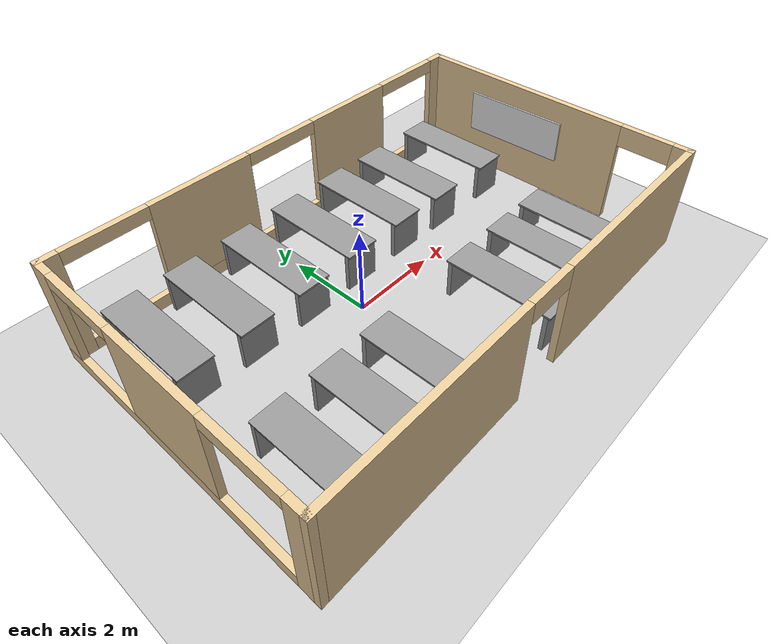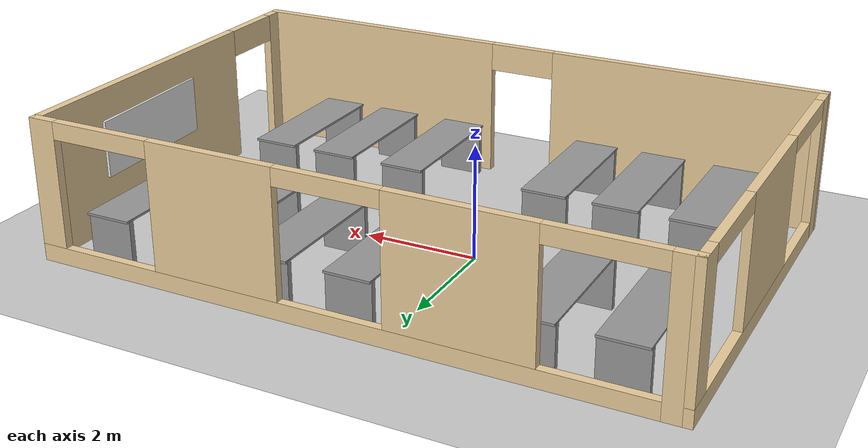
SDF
<sdf version="1.6">
 <world name="default">
  <light name="sun" type="directional">
   <pose>0 0 10 0 -0 0</pose>
   <diffuse>0.8 0.8 0.8 1</diffuse>
   <specular>0.1 0.1 0.1 1</specular>
   <attenuation>
    <range>1000</range>
    <constant>0.9</constant>
    <linear>0.01</linear>
    <quadratic>0.001</quadratic>
   </attenuation>
   <direction>-0.5 0.5 -1</direction>
  </light>
  <model name="ground_plane">
   <static>1</static>
   <link name="link">
    <collision name="collision">
     <geometry><plane><normal>0 0 1</normal><size>100 100</size></plane></geometry>
     <surface><friction><ode><mu>100</mu><mu2>50</mu2></ode></friction></surface>
    </collision>
    <visual name="visual">
     <cast_shadows>0</cast_shadows>
     <geometry><plane><normal>0 0 1</normal><size>100 100</size></plane></geometry>
     <material>
      <script><uri>file://media/materials/scripts/gazebo.material</uri><name>Gazebo/Grey</name></script>
     </material>
    </visual>
   </link>
  </model>
  <gravity>0 0 -9.8</gravity>
  <magnetic_field>6e-06 2.3e-05 -4.2e-05</magnetic_field>
  <atmosphere type="adiabatic"/>
  <physics name="default_physics" default="0" type="ode">
   <max_step_size>0.001</max_step_size>
   <real_time_factor>1</real_time_factor>
   <real_time_update_rate>1000</real_time_update_rate>
  </physics>
  <scene><ambient>0.4 0.4 0.4 1</ambient><background>0.7 0.7 0.7 1</background><shadows>1</shadows></scene>
  <spherical_coordinates>
   <surface_model>EARTH_WGS84</surface_model>
   <latitude_deg>0</latitude_deg>
   <longitude_deg>0</longitude_deg>
   <elevation>0</elevation>
   <heading_deg>0</heading_deg>
  </spherical_coordinates>
  <model name="labAlfa4">
   <pose>0.76702 -0.263718 0 0 -0 0</pose>
   <link name="Wall_25">
    <pose>-5.425 0 0 0 -0 1.5708</pose>
    <visual name="Wall_25_Visual_0">
     <pose>-3.25328 0 1.25 0 -0 0</pose>
     <geometry><box><size>0.493444 0.15 2.5</size></box></geometry>
     <material>
      <script><uri>file://media/materials/scripts/gazebo.material</uri><name>Gazebo/Grey</name></script>
      <ambient>0.921569 0.807843 0.615686 1</ambient>
     </material>
    </visual>
    <collision name="Wall_25_Collision_0">
     <geometry><box><size>0.493444 0.15 2.5</size></box></geometry>
     <pose>-3.25328 0 1.25 0 -0 0</pose>
    </collision>
    <visual name="Wall_25_Visual_1">
     <pose>0.246722 0 0.15 0 -0 0</pose>
     <geometry><box><size>6.50656 0.15 0.3</size></box></geometry>
     <material>
      <script><uri>file://media/materials/scripts/gazebo.material</uri><name>Gazebo/Grey</name></script>
      <ambient>0.921569 0.807843 0.615686 1</ambient>
     </material>
    </visual>
    <collision name="Wall_25_Collision_1">
     <geometry><box><size>6.50656 0.15 0.3</size></box></geometry>
     <pose>0.246722 0 0.15 0 -0 0</pose>
    </collision>
    <visual name="Wall_25_Visual_2">
     <pose>-0.00167 0 1.4 0 -0 0</pose>
     <geometry><box><size>2.40977 0.15 2.2</size></box></geometry>
     <material>
      <script><uri>file://media/materials/scripts/gazebo.material</uri><name>Gazebo/Grey</name></script>
      <ambient>0.921569 0.807843 0.615686 1</ambient>
     </material>
    </visual>
    <collision name="Wall_25_Collision_2">
     <geometry><box><size>2.40977 0.15 2.2</size></box></geometry>
     <pose>-0.00167 0 1.4 0 -0 0</pose>
    </collision>
    <visual name="Wall_25_Visual_3">
     <pose>3.25161 0 1.4 0 -0 0</pose>
     <geometry><box><size>0.496785 0.15 2.2</size></box></geometry>
     <material>
      <script><uri>file://media/materials/scripts/gazebo.material</uri><name>Gazebo/Grey</name></script>
      <ambient>0.921569 0.807843 0.615686 1</ambient>
     </material>
    </visual>
    <collision name="Wall_25_Collision_3">
     <geometry><box><size>0.496785 0.15 2.2</size></box></geometry>
     <pose>3.25161 0 1.4 0 -0 0</pose>
    </collision>
    <visual name="Wall_25_Visual_4">
     <pose>-2.10656 0 2.35 0 -0 0</pose>
     <geometry><box><size>1.8 0.15 0.3</size></box></geometry>
     <material>
      <script><uri>file://media/materials/scripts/gazebo.material</uri><name>Gazebo/Grey</name></script>
      <ambient>0.921569 0.807843 0.615686 1</ambient>
     </material>
    </visual>
    <collision name="Wall_25_Collision_4">
     <geometry><box><size>1.8 0.15 0.3</size></box></geometry>
     <pose>-2.10656 0 2.35 0 -0 0</pose>
    </collision>
    <visual name="Wall_25_Visual_5">
     <pose>2.10322 0 2.35 0 -0 0</pose>
     <geometry><box><size>1.8 0.15 0.3</size></box></geometry>
     <material>
      <script><uri>file://media/materials/scripts/gazebo.material</uri><name>Gazebo/Grey</name></script>
      <ambient>0.921569 0.807843 0.615686 1</ambient>
     </material>
    </visual>
    <collision name="Wall_25_Collision_5">
     <geometry><box><size>1.8 0.15 0.3</size></box></geometry>
     <pose>2.10322 0 2.35 0 -0 0</pose>
    </collision>
   </link>
   <link name="Wall_26">
    <pose>0 3.425 0 0 -0 0</pose>
    <visual name="Wall_26_Visual_0">
     <pose>-5.27641 0 1.25 0 -0 0</pose>
     <geometry><box><size>0.447183 0.15 2.5</size></box></geometry>
     <material>
      <script><uri>file://media/materials/scripts/gazebo.material</uri><name>Gazebo/Grey</name></script>
      <ambient>0.921569 0.807843 0.615686 1</ambient>
     </material>
    </visual>
    <collision name="Wall_26_Collision_0">
     <geometry><box><size>0.447183 0.15 2.5</size></box></geometry>
     <pose>-5.27641 0 1.25 0 -0 0</pose>
    </collision>
    <visual name="Wall_26_Visual_1">
     <pose>0.223592 0 0.15 0 -0 0</pose>
     <geometry><box><size>10.5528 0.15 0.3</size></box></geometry>
     <material>
      <script><uri>file://media/materials/scripts/gazebo.material</uri><name>Gazebo/Grey</name></script>
      <ambient>0.921569 0.807843 0.615686 1</ambient>
     </material>
    </visual>
    <collision name="Wall_26_Collision_1">
     <geometry><box><size>10.5528 0.15 0.3</size></box></geometry>
     <pose>0.223592 0 0.15 0 -0 0</pose>
    </collision>
    <visual name="Wall_26_Visual_2">
     <pose>-2.04793 0 1.4 0 -0 0</pose>
     <geometry><box><size>2.40977 0.15 2.2</size></box></geometry>
     <material>
      <script><uri>file://media/materials/scripts/gazebo.material</uri><name>Gazebo/Grey</name></script>
      <ambient>0.921569 0.807843 0.615686 1</ambient>
     </material>
    </visual>
    <collision name="Wall_26_Collision_2">
     <geometry><box><size>2.40977 0.15 2.2</size></box></geometry>
     <pose>-2.04793 0 1.4 0 -0 0</pose>
    </collision>
    <visual name="Wall_26_Visual_3">
     <pose>2.09245 0 1.4 0 -0 0</pose>
     <geometry><box><size>2.27099 0.15 2.2</size></box></geometry>
     <material>
      <script><uri>file://media/materials/scripts/gazebo.material</uri><name>Gazebo/Grey</name></script>
      <ambient>0.921569 0.807843 0.615686 1</ambient>
     </material>
    </visual>
    <collision name="Wall_26_Collision_3">
     <geometry><box><size>2.27099 0.15 2.2</size></box></geometry>
     <pose>2.09245 0 1.4 0 -0 0</pose>
    </collision>
    <visual name="Wall_26_Visual_4">
     <pose>5.26397 0 1.4 0 -0 0</pose>
     <geometry><box><size>0.472059 0.15 2.2</size></box></geometry>
     <material>
      <script><uri>file://media/materials/scripts/gazebo.material</uri><name>Gazebo/Grey</name></script>
      <ambient>0.921569 0.807843 0.615686 1</ambient>
     </material>
    </visual>
    <collision name="Wall_26_Collision_4">
     <geometry><box><size>0.472059 0.15 2.2</size></box></geometry>
     <pose>5.26397 0 1.4 0 -0 0</pose>
    </collision>
    <visual name="Wall_26_Visual_5">
     <pose>-4.15282 0 2.35 0 -0 0</pose>
     <geometry><box><size>1.8 0.15 0.3</size></box></geometry>
     <material>
      <script><uri>file://media/materials/scripts/gazebo.material</uri><name>Gazebo/Grey</name></script>
      <ambient>0.921569 0.807843 0.615686 1</ambient>
     </material>
    </visual>
    <collision name="Wall_26_Collision_5">
     <geometry><box><size>1.8 0.15 0.3</size></box></geometry>
     <pose>-4.15282 0 2.35 0 -0 0</pose>
    </collision>
    <visual name="Wall_26_Visual_6">
     <pose>0.056954 0 2.35 0 -0 0</pose>
     <geometry><box><size>1.8 0.15 0.3</size></box></geometry>
     <material>
      <script><uri>file://media/materials/scripts/gazebo.material</uri><name>Gazebo/Grey</name></script>
      <ambient>0.921569 0.807843 0.615686 1</ambient>
     </material>
    </visual>
    <collision name="Wall_26_Collision_6">
     <geometry><box><size>1.8 0.15 0.3</size></box></geometry>
     <pose>0.056954 0 2.35 0 -0 0</pose>
    </collision>
    <visual name="Wall_26_Visual_7">
     <pose>4.12794 0 2.35 0 -0 0</pose>
     <geometry><box><size>1.8 0.15 0.3</size></box></geometry>
     <material>
      <script><uri>file://media/materials/scripts/gazebo.material</uri><name>Gazebo/Grey</name></script>
      <ambient>0.921569 0.807843 0.615686 1</ambient>
     </material>
    </visual>
    <collision name="Wall_26_Collision_7">
     <geometry><box><size>1.8 0.15 0.3</size></box></geometry>
     <pose>4.12794 0 2.35 0 -0 0</pose>
    </collision>
   </link>
   <link name="Wall_27">
    <pose>5.425 0 0 0 0 -1.5708</pose>
    <visual name="Wall_27_Visual_0">
     <pose>-0.823243 0 1.25 0 -0 0</pose>
     <geometry><box><size>5.35351 0.15 2.5</size></box></geometry>
     <material>
      <script><uri>file://media/materials/scripts/gazebo.material</uri><name>Gazebo/Grey</name></script>
      <ambient>0.921569 0.807843 0.615686 1</ambient>
     </material>
    </visual>
    <collision name="Wall_27_Collision_0">
     <geometry><box><size>5.35351 0.15 2.5</size></box></geometry>
     <pose>-0.823243 0 1.25 0 -0 0</pose>
    </collision>
    <visual name="Wall_27_Visual_1">
     <pose>3.27676 0 1.25 0 -0 0</pose>
     <geometry><box><size>0.446485 0.15 2.5</size></box></geometry>
     <material>
      <script><uri>file://media/materials/scripts/gazebo.material</uri><name>Gazebo/Grey</name></script>
      <ambient>0.921569 0.807843 0.615686 1</ambient>
     </material>
    </visual>
    <collision name="Wall_27_Collision_1">
     <geometry><box><size>0.446485 0.15 2.5</size></box></geometry>
     <pose>3.27676 0 1.25 0 -0 0</pose>
    </collision>
    <visual name="Wall_27_Visual_2">
     <pose>2.45351 0 2.25 0 -0 0</pose>
     <geometry><box><size>1.2 0.15 0.5</size></box></geometry>
     <material>
      <script><uri>file://media/materials/scripts/gazebo.material</uri><name>Gazebo/Grey</name></script>
      <ambient>0.921569 0.807843 0.615686 1</ambient>
     </material>
    </visual>
    <collision name="Wall_27_Collision_2">
     <geometry><box><size>1.2 0.15 0.5</size></box></geometry>
     <pose>2.45351 0 2.25 0 -0 0</pose>
    </collision>
   </link>
   <link name="Wall_28">
    <pose>0 -3.425 0 0 -0 3.14159</pose>
    <visual name="Wall_28_Visual_0">
     <pose>-3.06691 0 1.25 0 -0 0</pose>
     <geometry><box><size>4.86618 0.15 2.5</size></box></geometry>
     <material>
      <script><uri>file://media/materials/scripts/gazebo.material</uri><name>Gazebo/Grey</name></script>
      <ambient>0.921569 0.807843 0.615686 1</ambient>
     </material>
    </visual>
    <collision name="Wall_28_Collision_0">
     <geometry><box><size>4.86618 0.15 2.5</size></box></geometry>
     <pose>-3.06691 0 1.25 0 -0 0</pose>
    </collision>
    <visual name="Wall_28_Visual_1">
     <pose>3.03309 0 1.25 0 -0 0</pose>
     <geometry><box><size>4.93382 0.15 2.5</size></box></geometry>
     <material>
      <script><uri>file://media/materials/scripts/gazebo.material</uri><name>Gazebo/Grey</name></script>
      <ambient>0.921569 0.807843 0.615686 1</ambient>
     </material>
    </visual>
    <collision name="Wall_28_Collision_1">
     <geometry><box><size>4.93382 0.15 2.5</size></box></geometry>
     <pose>3.03309 0 1.25 0 -0 0</pose>
    </collision>
    <visual name="Wall_28_Visual_2">
     <pose>-0.033823 0 2.25 0 -0 0</pose>
     <geometry><box><size>1.2 0.15 0.5</size></box></geometry>
     <material>
      <script><uri>file://media/materials/scripts/gazebo.material</uri><name>Gazebo/Grey</name></script>
      <ambient>0.921569 0.807843 0.615686 1</ambient>
     </material>
    </visual>
    <collision name="Wall_28_Collision_2">
     <geometry><box><size>1.2 0.15 0.5</size></box></geometry>
     <pose>-0.033823 0 2.25 0 -0 0</pose>
    </collision>
   </link>
   <static>1</static>
  </model>
  <model name="table_clone_2_clone">
   <link name="link">
    <inertial>
     <inertia><ixx>1</ixx><ixy>0</ixy><ixz>0</ixz><iyy>1</iyy><iyz>0</iyz><izz>1</izz></inertia>
     <mass>10</mass>
    </inertial>
    <visual name="visual1">
     <pose>0 0 0.95 0 -0 0</pose>
     <geometry><box><size>2.5 0.8 0.04</size></box></geometry>
     <material>
      <script><uri>file://media/materials/scripts/gazebo.material</uri><name>Gazebo/Grey</name></script>
      <ambient>1 1 1 1</ambient>
      <diffuse>1 1 1 1</diffuse>
      <specular>0.2 0.2 0.2 1</specular>
      <emissive>0 0 0 1</emissive>
      <shader type="vertex"><normal_map>__default__</normal_map></shader>
     </material>
    </visual>
    <visual name="ModelPreview_1::link::visual_12">
     <pose>1.15 0 0.5 0 -0 0</pose>
     <geometry><box><size>0.1 0.8 0.9</size></box></geometry>
     <material>
      <script><uri>file://media/materials/scripts/gazebo.material</uri><name>Gazebo/Grey</name></script>
      <ambient>0.3 0.3 0.3 1</ambient>
      <diffuse>0.7 0.7 0.7 1</diffuse>
      <specular>0.01 0.01 0.01 1</specular>
      <emissive>0 0 0 1</emissive>
      <shader type="vertex"><normal_map>__default__</normal_map></shader>
     </material>
    </visual>
    <visual name="back_right_leg">
     <pose>-1.15 0 0.5 0 -0 0</pose>
     <geometry><box><size>0.1 0.8 0.9</size></box></geometry>
     <material>
      <script><uri>file://media/materials/scripts/gazebo.material</uri><name>Gazebo/Grey</name></script>
      <ambient>0.3 0.3 0.3 1</ambient>
      <diffuse>0.7 0.7 0.7 1</diffuse>
      <specular>0.01 0.01 0.01 1</specular>
      <emissive>0 0 0 1</emissive>
      <shader type="vertex"><normal_map>__default__</normal_map></shader>
     </material>
    </visual>
    <collision name="collision_7">
     <pose>1.15 0 0.5 0 -0 0</pose>
     <geometry><box><size>0.1 0.8 0.9</size></box></geometry>
     <surface>
      <friction>
       <ode><mu>1</mu><mu2>1</mu2><fdir1>0 0 0</fdir1><slip1>0</slip1><slip2>0</slip2></ode>
       <torsional>
        <coefficient>1</coefficient>
        <patch_radius>0</patch_radius>
        <surface_radius>0</surface_radius>
        <use_patch_radius>1</use_patch_radius>
        <ode><slip>0</slip></ode>
       </torsional>
      </friction>
      <bounce><restitution_coefficient>0</restitution_coefficient><threshold>1e+06</threshold></bounce>
      <contact>
       <collide_without_contact>0</collide_without_contact>
       <collide_without_contact_bitmask>1</collide_without_contact_bitmask>
       <collide_bitmask>1</collide_bitmask>
       <ode>
        <soft_cfm>0</soft_cfm>
        <soft_erp>0.2</soft_erp>
        <kp>1e+13</kp>
        <kd>1</kd>
        <max_vel>0.01</max_vel>
        <min_depth>0</min_depth>
       </ode>
       <bullet>
        <split_impulse>1</split_impulse>
        <split_impulse_penetration_threshold>-0.01</split_impulse_penetration_threshold>
        <soft_cfm>0</soft_cfm>
        <soft_erp>0.2</soft_erp>
        <kp>1e+13</kp>
        <kd>1</kd>
       </bullet>
      </contact>
     </surface>
    </collision>
    <collision name="surface">
     <pose>0 0 0.95 0 -0 0</pose>
     <geometry><box><size>2.5 0.8 0.03</size></box></geometry>
     <surface>
      <friction>
       <ode><mu>0.6</mu><mu2>0.6</mu2><fdir1>0 0 0</fdir1><slip1>0</slip1><slip2>0</slip2></ode>
       <torsional>
        <coefficient>1</coefficient>
        <patch_radius>0</patch_radius>
        <surface_radius>0</surface_radius>
        <use_patch_radius>1</use_patch_radius>
        <ode><slip>0</slip></ode>
       </torsional>
      </friction>
      <bounce><restitution_coefficient>0</restitution_coefficient><threshold>1e+06</threshold></bounce>
      <contact>
       <collide_without_contact>0</collide_without_contact>
       <collide_without_contact_bitmask>1</collide_without_contact_bitmask>
       <collide_bitmask>1</collide_bitmask>
       <ode>
        <soft_cfm>0</soft_cfm>
        <soft_erp>0.2</soft_erp>
        <kp>1e+13</kp>
        <kd>1</kd>
        <max_vel>0.01</max_vel>
        <min_depth>0</min_depth>
       </ode>
       <bullet>
        <split_impulse>1</split_impulse>
        <split_impulse_penetration_threshold>-0.01</split_impulse_penetration_threshold>
        <soft_cfm>0</soft_cfm>
        <soft_erp>0.2</soft_erp>
        <kp>1e+13</kp>
        <kd>1</kd>
       </bullet>
      </contact>
     </surface>
    </collision>
    <collision name="collision_5">
     <pose>-1.15 0 0.5 0 -0 0</pose>
     <geometry><box><size>0.1 0.8 0.9</size></box></geometry>
     <surface>
      <friction>
       <ode><mu>1</mu><mu2>1</mu2><fdir1>0 0 0</fdir1><slip1>0</slip1><slip2>0</slip2></ode>
       <torsional>
        <coefficient>1</coefficient>
        <patch_radius>0</patch_radius>
        <surface_radius>0</surface_radius>
        <use_patch_radius>1</use_patch_radius>
        <ode><slip>0</slip></ode>
       </torsional>
      </friction>
      <bounce><restitution_coefficient>0</restitution_coefficient><threshold>1e+06</threshold></bounce>
      <contact>
       <collide_without_contact>0</collide_without_contact>
       <collide_without_contact_bitmask>1</collide_without_contact_bitmask>
       <collide_bitmask>1</collide_bitmask>
       <ode>
        <soft_cfm>0</soft_cfm>
        <soft_erp>0.2</soft_erp>
        <kp>1e+13</kp>
        <kd>1</kd>
        <max_vel>0.01</max_vel>
        <min_depth>0</min_depth>
       </ode>
       <bullet>
        <split_impulse>1</split_impulse>
        <split_impulse_penetration_threshold>-0.01</split_impulse_penetration_threshold>
        <soft_cfm>0</soft_cfm>
        <soft_erp>0.2</soft_erp>
        <kp>1e+13</kp>
        <kd>1</kd>
       </bullet>
      </contact>
     </surface>
    </collision>
   </link>
   <static>0</static>
   <pose>4.5122 -2.24052 -0.050008 -2e-05 -0 -1.57004</pose>
  </model>
  <model name="table_clone_2_clone_0">
   <link name="link">
    <inertial>
     <inertia><ixx>1</ixx><ixy>0</ixy><ixz>0</ixz><iyy>1</iyy><iyz>0</iyz><izz>1</izz></inertia>
     <mass>10</mass>
    </inertial>
    <visual name="visual1">
     <pose>0 0 0.95 0 -0 0</pose>
     <geometry><box><size>2.5 0.8 0.04</size></box></geometry>
     <material>
      <script><uri>file://media/materials/scripts/gazebo.material</uri><name>Gazebo/Grey</name></script>
      <ambient>1 1 1 1</ambient>
      <diffuse>1 1 1 1</diffuse>
      <specular>0.2 0.2 0.2 1</specular>
      <emissive>0 0 0 1</emissive>
      <shader type="vertex"><normal_map>__default__</normal_map></shader>
     </material>
    </visual>
    <visual name="ModelPreview_1::link::visual_12">
     <pose>1.15 0 0.5 0 -0 0</pose>
     <geometry><box><size>0.1 0.8 0.9</size></box></geometry>
     <material>
      <script><uri>file://media/materials/scripts/gazebo.material</uri><name>Gazebo/Grey</name></script>
      <ambient>0.3 0.3 0.3 1</ambient>
      <diffuse>0.7 0.7 0.7 1</diffuse>
      <specular>0.01 0.01 0.01 1</specular>
      <emissive>0 0 0 1</emissive>
      <shader type="vertex"><normal_map>__default__</normal_map></shader>
     </material>
    </visual>
    <visual name="back_right_leg">
     <pose>-1.15 0 0.5 0 -0 0</pose>
     <geometry><box><size>0.1 0.8 0.9</size></box></geometry>
     <material>
      <script><uri>file://media/materials/scripts/gazebo.material</uri><name>Gazebo/Grey</name></script>
      <ambient>0.3 0.3 0.3 1</ambient>
      <diffuse>0.7 0.7 0.7 1</diffuse>
      <specular>0.01 0.01 0.01 1</specular>
      <emissive>0 0 0 1</emissive>
      <shader type="vertex"><normal_map>__default__</normal_map></shader>
     </material>
    </visual>
    <collision name="collision_7">
     <pose>1.15 0 0.5 0 -0 0</pose>
     <geometry><box><size>0.1 0.8 0.9</size></box></geometry>
     <surface>
      <friction>
       <ode><mu>1</mu><mu2>1</mu2><fdir1>0 0 0</fdir1><slip1>0</slip1><slip2>0</slip2></ode>
       <torsional>
        <coefficient>1</coefficient>
        <patch_radius>0</patch_radius>
        <surface_radius>0</surface_radius>
        <use_patch_radius>1</use_patch_radius>
        <ode><slip>0</slip></ode>
       </torsional>
      </friction>
      <bounce><restitution_coefficient>0</restitution_coefficient><threshold>1e+06</threshold></bounce>
      <contact>
       <collide_without_contact>0</collide_without_contact>
       <collide_without_contact_bitmask>1</collide_without_contact_bitmask>
       <collide_bitmask>1</collide_bitmask>
       <ode>
        <soft_cfm>0</soft_cfm>
        <soft_erp>0.2</soft_erp>
        <kp>1e+13</kp>
        <kd>1</kd>
        <max_vel>0.01</max_vel>
        <min_depth>0</min_depth>
       </ode>
       <bullet>
        <split_impulse>1</split_impulse>
        <split_impulse_penetration_threshold>-0.01</split_impulse_penetration_threshold>
        <soft_cfm>0</soft_cfm>
        <soft_erp>0.2</soft_erp>
        <kp>1e+13</kp>
        <kd>1</kd>
       </bullet>
      </contact>
     </surface>
    </collision>
    <collision name="surface">
     <pose>0 0 0.95 0 -0 0</pose>
     <geometry><box><size>2.5 0.8 0.03</size></box></geometry>
     <surface>
      <friction>
       <ode><mu>0.6</mu><mu2>0.6</mu2><fdir1>0 0 0</fdir1><slip1>0</slip1><slip2>0</slip2></ode>
       <torsional>
        <coefficient>1</coefficient>
        <patch_radius>0</patch_radius>
        <surface_radius>0</surface_radius>
        <use_patch_radius>1</use_patch_radius>
        <ode><slip>0</slip></ode>
       </torsional>
      </friction>
      <bounce><restitution_coefficient>0</restitution_coefficient><threshold>1e+06</threshold></bounce>
      <contact>
       <collide_without_contact>0</collide_without_contact>
       <collide_without_contact_bitmask>1</collide_without_contact_bitmask>
       <collide_bitmask>1</collide_bitmask>
       <ode>
        <soft_cfm>0</soft_cfm>
        <soft_erp>0.2</soft_erp>
        <kp>1e+13</kp>
        <kd>1</kd>
        <max_vel>0.01</max_vel>
        <min_depth>0</min_depth>
       </ode>
       <bullet>
        <split_impulse>1</split_impulse>
        <split_impulse_penetration_threshold>-0.01</split_impulse_penetration_threshold>
        <soft_cfm>0</soft_cfm>
        <soft_erp>0.2</soft_erp>
        <kp>1e+13</kp>
        <kd>1</kd>
       </bullet>
      </contact>
     </surface>
    </collision>
    <collision name="collision_5">
     <pose>-1.15 0 0.5 0 -0 0</pose>
     <geometry><box><size>0.1 0.8 0.9</size></box></geometry>
     <surface>
      <friction>
       <ode><mu>1</mu><mu2>1</mu2><fdir1>0 0 0</fdir1><slip1>0</slip1><slip2>0</slip2></ode>
       <torsional>
        <coefficient>1</coefficient>
        <patch_radius>0</patch_radius>
        <surface_radius>0</surface_radius>
        <use_patch_radius>1</use_patch_radius>
        <ode><slip>0</slip></ode>
       </torsional>
      </friction>
      <bounce><restitution_coefficient>0</restitution_coefficient><threshold>1e+06</threshold></bounce>
      <contact>
       <collide_without_contact>0</collide_without_contact>
       <collide_without_contact_bitmask>1</collide_without_contact_bitmask>
       <collide_bitmask>1</collide_bitmask>
       <ode>
        <soft_cfm>0</soft_cfm>
        <soft_erp>0.2</soft_erp>
        <kp>1e+13</kp>
        <kd>1</kd>
        <max_vel>0.01</max_vel>
        <min_depth>0</min_depth>
       </ode>
       <bullet>
        <split_impulse>1</split_impulse>
        <split_impulse_penetration_threshold>-0.01</split_impulse_penetration_threshold>
        <soft_cfm>0</soft_cfm>
        <soft_erp>0.2</soft_erp>
        <kp>1e+13</kp>
        <kd>1</kd>
       </bullet>
      </contact>
     </surface>
    </collision>
   </link>
   <static>0</static>
   <pose>5.07585 1.76138 -0.050008 -2e-05 -0 -1.57004</pose>
  </model>
  <model name="table_clone_2_clone_1">
   <link name="link">
    <inertial>
     <inertia><ixx>1</ixx><ixy>0</ixy><ixz>0</ixz><iyy>1</iyy><iyz>0</iyz><izz>1</izz></inertia>
     <mass>10</mass>
    </inertial>
    <visual name="visual1">
     <pose>0 0 0.95 0 -0 0</pose>
     <geometry><box><size>2.5 0.8 0.04</size></box></geometry>
     <material>
      <script><uri>file://media/materials/scripts/gazebo.material</uri><name>Gazebo/Grey</name></script>
      <ambient>1 1 1 1</ambient>
      <diffuse>1 1 1 1</diffuse>
      <specular>0.2 0.2 0.2 1</specular>
      <emissive>0 0 0 1</emissive>
      <shader type="vertex"><normal_map>__default__</normal_map></shader>
     </material>
    </visual>
    <visual name="ModelPreview_1::link::visual_12">
     <pose>1.15 0 0.5 0 -0 0</pose>
     <geometry><box><size>0.1 0.8 0.9</size></box></geometry>
     <material>
      <script><uri>file://media/materials/scripts/gazebo.material</uri><name>Gazebo/Grey</name></script>
      <ambient>0.3 0.3 0.3 1</ambient>
      <diffuse>0.7 0.7 0.7 1</diffuse>
      <specular>0.01 0.01 0.01 1</specular>
      <emissive>0 0 0 1</emissive>
      <shader type="vertex"><normal_map>__default__</normal_map></shader>
     </material>
    </visual>
    <visual name="back_right_leg">
     <pose>-1.15 0 0.5 0 -0 0</pose>
     <geometry><box><size>0.1 0.8 0.9</size></box></geometry>
     <material>
      <script><uri>file://media/materials/scripts/gazebo.material</uri><name>Gazebo/Grey</name></script>
      <ambient>0.3 0.3 0.3 1</ambient>
      <diffuse>0.7 0.7 0.7 1</diffuse>
      <specular>0.01 0.01 0.01 1</specular>
      <emissive>0 0 0 1</emissive>
      <shader type="vertex"><normal_map>__default__</normal_map></shader>
     </material>
    </visual>
    <collision name="collision_7">
     <pose>1.15 0 0.5 0 -0 0</pose>
     <geometry><box><size>0.1 0.8 0.9</size></box></geometry>
     <surface>
      <friction>
       <ode><mu>1</mu><mu2>1</mu2><fdir1>0 0 0</fdir1><slip1>0</slip1><slip2>0</slip2></ode>
       <torsional>
        <coefficient>1</coefficient>
        <patch_radius>0</patch_radius>
        <surface_radius>0</surface_radius>
        <use_patch_radius>1</use_patch_radius>
        <ode><slip>0</slip></ode>
       </torsional>
      </friction>
      <bounce><restitution_coefficient>0</restitution_coefficient><threshold>1e+06</threshold></bounce>
      <contact>
       <collide_without_contact>0</collide_without_contact>
       <collide_without_contact_bitmask>1</collide_without_contact_bitmask>
       <collide_bitmask>1</collide_bitmask>
       <ode>
        <soft_cfm>0</soft_cfm>
        <soft_erp>0.2</soft_erp>
        <kp>1e+13</kp>
        <kd>1</kd>
        <max_vel>0.01</max_vel>
        <min_depth>0</min_depth>
       </ode>
       <bullet>
        <split_impulse>1</split_impulse>
        <split_impulse_penetration_threshold>-0.01</split_impulse_penetration_threshold>
        <soft_cfm>0</soft_cfm>
        <soft_erp>0.2</soft_erp>
        <kp>1e+13</kp>
        <kd>1</kd>
       </bullet>
      </contact>
     </surface>
    </collision>
    <collision name="surface">
     <pose>0 0 0.95 0 -0 0</pose>
     <geometry><box><size>2.5 0.8 0.03</size></box></geometry>
     <surface>
      <friction>
       <ode><mu>0.6</mu><mu2>0.6</mu2><fdir1>0 0 0</fdir1><slip1>0</slip1><slip2>0</slip2></ode>
       <torsional>
        <coefficient>1</coefficient>
        <patch_radius>0</patch_radius>
        <surface_radius>0</surface_radius>
        <use_patch_radius>1</use_patch_radius>
        <ode><slip>0</slip></ode>
       </torsional>
      </friction>
      <bounce><restitution_coefficient>0</restitution_coefficient><threshold>1e+06</threshold></bounce>
      <contact>
       <collide_without_contact>0</collide_without_contact>
       <collide_without_contact_bitmask>1</collide_without_contact_bitmask>
       <collide_bitmask>1</collide_bitmask>
       <ode>
        <soft_cfm>0</soft_cfm>
        <soft_erp>0.2</soft_erp>
        <kp>1e+13</kp>
        <kd>1</kd>
        <max_vel>0.01</max_vel>
        <min_depth>0</min_depth>
       </ode>
       <bullet>
        <split_impulse>1</split_impulse>
        <split_impulse_penetration_threshold>-0.01</split_impulse_penetration_threshold>
        <soft_cfm>0</soft_cfm>
        <soft_erp>0.2</soft_erp>
        <kp>1e+13</kp>
        <kd>1</kd>
       </bullet>
      </contact>
     </surface>
    </collision>
    <collision name="collision_5">
     <pose>-1.15 0 0.5 0 -0 0</pose>
     <geometry><box><size>0.1 0.8 0.9</size></box></geometry>
     <surface>
      <friction>
       <ode><mu>1</mu><mu2>1</mu2><fdir1>0 0 0</fdir1><slip1>0</slip1><slip2>0</slip2></ode>
       <torsional>
        <coefficient>1</coefficient>
        <patch_radius>0</patch_radius>
        <surface_radius>0</surface_radius>
        <use_patch_radius>1</use_patch_radius>
        <ode><slip>0</slip></ode>
       </torsional>
      </friction>
      <bounce><restitution_coefficient>0</restitution_coefficient><threshold>1e+06</threshold></bounce>
      <contact>
       <collide_without_contact>0</collide_without_contact>
       <collide_without_contact_bitmask>1</collide_without_contact_bitmask>
       <collide_bitmask>1</collide_bitmask>
       <ode>
        <soft_cfm>0</soft_cfm>
        <soft_erp>0.2</soft_erp>
        <kp>1e+13</kp>
        <kd>1</kd>
        <max_vel>0.01</max_vel>
        <min_depth>0</min_depth>
       </ode>
       <bullet>
        <split_impulse>1</split_impulse>
        <split_impulse_penetration_threshold>-0.01</split_impulse_penetration_threshold>
        <soft_cfm>0</soft_cfm>
        <soft_erp>0.2</soft_erp>
        <kp>1e+13</kp>
        <kd>1</kd>
       </bullet>
      </contact>
     </surface>
    </collision>
   </link>
   <static>0</static>
   <pose>-0.813096 1.74776 -0.050005 -1.2e-05 0 -1.57001</pose>
  </model>
  <model name="table_clone_2_clone_2">
   <link name="link">
    <inertial>
     <inertia><ixx>1</ixx><ixy>0</ixy><ixz>0</ixz><iyy>1</iyy><iyz>0</iyz><izz>1</izz></inertia>
     <mass>10</mass>
    </inertial>
    <visual name="visual1">
     <pose>0 0 0.95 0 -0 0</pose>
     <geometry><box><size>2.5 0.8 0.04</size></box></geometry>
     <material>
      <script><uri>file://media/materials/scripts/gazebo.material</uri><name>Gazebo/Grey</name></script>
      <ambient>1 1 1 1</ambient>
      <diffuse>1 1 1 1</diffuse>
      <specular>0.2 0.2 0.2 1</specular>
      <emissive>0 0 0 1</emissive>
      <shader type="vertex"><normal_map>__default__</normal_map></shader>
     </material>
    </visual>
    <visual name="ModelPreview_1::link::visual_12">
     <pose>1.15 0 0.5 0 -0 0</pose>
     <geometry><box><size>0.1 0.8 0.9</size></box></geometry>
     <material>
      <script><uri>file://media/materials/scripts/gazebo.material</uri><name>Gazebo/Grey</name></script>
      <ambient>0.3 0.3 0.3 1</ambient>
      <diffuse>0.7 0.7 0.7 1</diffuse>
      <specular>0.01 0.01 0.01 1</specular>
      <emissive>0 0 0 1</emissive>
      <shader type="vertex"><normal_map>__default__</normal_map></shader>
     </material>
    </visual>
    <visual name="back_right_leg">
     <pose>-1.15 0 0.5 0 -0 0</pose>
     <geometry><box><size>0.1 0.8 0.9</size></box></geometry>
     <material>
      <script><uri>file://media/materials/scripts/gazebo.material</uri><name>Gazebo/Grey</name></script>
      <ambient>0.3 0.3 0.3 1</ambient>
      <diffuse>0.7 0.7 0.7 1</diffuse>
      <specular>0.01 0.01 0.01 1</specular>
      <emissive>0 0 0 1</emissive>
      <shader type="vertex"><normal_map>__default__</normal_map></shader>
     </material>
    </visual>
    <collision name="collision_7">
     <pose>1.15 0 0.5 0 -0 0</pose>
     <geometry><box><size>0.1 0.8 0.9</size></box></geometry>
     <surface>
      <friction>
       <ode><mu>1</mu><mu2>1</mu2><fdir1>0 0 0</fdir1><slip1>0</slip1><slip2>0</slip2></ode>
       <torsional>
        <coefficient>1</coefficient>
        <patch_radius>0</patch_radius>
        <surface_radius>0</surface_radius>
        <use_patch_radius>1</use_patch_radius>
        <ode><slip>0</slip></ode>
       </torsional>
      </friction>
      <bounce><restitution_coefficient>0</restitution_coefficient><threshold>1e+06</threshold></bounce>
      <contact>
       <collide_without_contact>0</collide_without_contact>
       <collide_without_contact_bitmask>1</collide_without_contact_bitmask>
       <collide_bitmask>1</collide_bitmask>
       <ode>
        <soft_cfm>0</soft_cfm>
        <soft_erp>0.2</soft_erp>
        <kp>1e+13</kp>
        <kd>1</kd>
        <max_vel>0.01</max_vel>
        <min_depth>0</min_depth>
       </ode>
       <bullet>
        <split_impulse>1</split_impulse>
        <split_impulse_penetration_threshold>-0.01</split_impulse_penetration_threshold>
        <soft_cfm>0</soft_cfm>
        <soft_erp>0.2</soft_erp>
        <kp>1e+13</kp>
        <kd>1</kd>
       </bullet>
      </contact>
     </surface>
    </collision>
    <collision name="surface">
     <pose>0 0 0.95 0 -0 0</pose>
     <geometry><box><size>2.5 0.8 0.03</size></box></geometry>
     <surface>
      <friction>
       <ode><mu>0.6</mu><mu2>0.6</mu2><fdir1>0 0 0</fdir1><slip1>0</slip1><slip2>0</slip2></ode>
       <torsional>
        <coefficient>1</coefficient>
        <patch_radius>0</patch_radius>
        <surface_radius>0</surface_radius>
        <use_patch_radius>1</use_patch_radius>
        <ode><slip>0</slip></ode>
       </torsional>
      </friction>
      <bounce><restitution_coefficient>0</restitution_coefficient><threshold>1e+06</threshold></bounce>
      <contact>
       <collide_without_contact>0</collide_without_contact>
       <collide_without_contact_bitmask>1</collide_without_contact_bitmask>
       <collide_bitmask>1</collide_bitmask>
       <ode>
        <soft_cfm>0</soft_cfm>
        <soft_erp>0.2</soft_erp>
        <kp>1e+13</kp>
        <kd>1</kd>
        <max_vel>0.01</max_vel>
        <min_depth>0</min_depth>
       </ode>
       <bullet>
        <split_impulse>1</split_impulse>
        <split_impulse_penetration_threshold>-0.01</split_impulse_penetration_threshold>
        <soft_cfm>0</soft_cfm>
        <soft_erp>0.2</soft_erp>
        <kp>1e+13</kp>
        <kd>1</kd>
       </bullet>
      </contact>
     </surface>
    </collision>
    <collision name="collision_5">
     <pose>-1.15 0 0.5 0 -0 0</pose>
     <geometry><box><size>0.1 0.8 0.9</size></box></geometry>
     <surface>
      <friction>
       <ode><mu>1</mu><mu2>1</mu2><fdir1>0 0 0</fdir1><slip1>0</slip1><slip2>0</slip2></ode>
       <torsional>
        <coefficient>1</coefficient>
        <patch_radius>0</patch_radius>
        <surface_radius>0</surface_radius>
        <use_patch_radius>1</use_patch_radius>
        <ode><slip>0</slip></ode>
       </torsional>
      </friction>
      <bounce><restitution_coefficient>0</restitution_coefficient><threshold>1e+06</threshold></bounce>
      <contact>
       <collide_without_contact>0</collide_without_contact>
       <collide_without_contact_bitmask>1</collide_without_contact_bitmask>
       <collide_bitmask>1</collide_bitmask>
       <ode>
        <soft_cfm>0</soft_cfm>
        <soft_erp>0.2</soft_erp>
        <kp>1e+13</kp>
        <kd>1</kd>
        <max_vel>0.01</max_vel>
        <min_depth>0</min_depth>
       </ode>
       <bullet>
        <split_impulse>1</split_impulse>
        <split_impulse_penetration_threshold>-0.01</split_impulse_penetration_threshold>
        <soft_cfm>0</soft_cfm>
        <soft_erp>0.2</soft_erp>
        <kp>1e+13</kp>
        <kd>1</kd>
       </bullet>
      </contact>
     </surface>
    </collision>
   </link>
   <static>0</static>
   <pose>2.05961 1.80575 -0.050008 -2e-05 -0 -1.57004</pose>
  </model>
  <model name="table_clone_2_clone_3">
   <link name="link">
    <inertial>
     <inertia><ixx>1</ixx><ixy>0</ixy><ixz>0</ixz><iyy>1</iyy><iyz>0</iyz><izz>1</izz></inertia>
     <mass>10</mass>
    </inertial>
    <visual name="visual1">
     <pose>0 0 0.95 0 -0 0</pose>
     <geometry><box><size>2.5 0.8 0.04</size></box></geometry>
     <material>
      <script><uri>file://media/materials/scripts/gazebo.material</uri><name>Gazebo/Grey</name></script>
      <ambient>1 1 1 1</ambient>
      <diffuse>1 1 1 1</diffuse>
      <specular>0.2 0.2 0.2 1</specular>
      <emissive>0 0 0 1</emissive>
      <shader type="vertex"><normal_map>__default__</normal_map></shader>
     </material>
    </visual>
    <visual name="ModelPreview_1::link::visual_12">
     <pose>1.15 0 0.5 0 -0 0</pose>
     <geometry><box><size>0.1 0.8 0.9</size></box></geometry>
     <material>
      <script><uri>file://media/materials/scripts/gazebo.material</uri><name>Gazebo/Grey</name></script>
      <ambient>0.3 0.3 0.3 1</ambient>
      <diffuse>0.7 0.7 0.7 1</diffuse>
      <specular>0.01 0.01 0.01 1</specular>
      <emissive>0 0 0 1</emissive>
      <shader type="vertex"><normal_map>__default__</normal_map></shader>
     </material>
    </visual>
    <visual name="back_right_leg">
     <pose>-1.15 0 0.5 0 -0 0</pose>
     <geometry><box><size>0.1 0.8 0.9</size></box></geometry>
     <material>
      <script><uri>file://media/materials/scripts/gazebo.material</uri><name>Gazebo/Grey</name></script>
      <ambient>0.3 0.3 0.3 1</ambient>
      <diffuse>0.7 0.7 0.7 1</diffuse>
      <specular>0.01 0.01 0.01 1</specular>
      <emissive>0 0 0 1</emissive>
      <shader type="vertex"><normal_map>__default__</normal_map></shader>
     </material>
    </visual>
    <collision name="collision_7">
     <pose>1.15 0 0.5 0 -0 0</pose>
     <geometry><box><size>0.1 0.8 0.9</size></box></geometry>
     <surface>
      <friction>
       <ode><mu>1</mu><mu2>1</mu2><fdir1>0 0 0</fdir1><slip1>0</slip1><slip2>0</slip2></ode>
       <torsional>
        <coefficient>1</coefficient>
        <patch_radius>0</patch_radius>
        <surface_radius>0</surface_radius>
        <use_patch_radius>1</use_patch_radius>
        <ode><slip>0</slip></ode>
       </torsional>
      </friction>
      <bounce><restitution_coefficient>0</restitution_coefficient><threshold>1e+06</threshold></bounce>
      <contact>
       <collide_without_contact>0</collide_without_contact>
       <collide_without_contact_bitmask>1</collide_without_contact_bitmask>
       <collide_bitmask>1</collide_bitmask>
       <ode>
        <soft_cfm>0</soft_cfm>
        <soft_erp>0.2</soft_erp>
        <kp>1e+13</kp>
        <kd>1</kd>
        <max_vel>0.01</max_vel>
        <min_depth>0</min_depth>
       </ode>
       <bullet>
        <split_impulse>1</split_impulse>
        <split_impulse_penetration_threshold>-0.01</split_impulse_penetration_threshold>
        <soft_cfm>0</soft_cfm>
        <soft_erp>0.2</soft_erp>
        <kp>1e+13</kp>
        <kd>1</kd>
       </bullet>
      </contact>
     </surface>
    </collision>
    <collision name="surface">
     <pose>0 0 0.95 0 -0 0</pose>
     <geometry><box><size>2.5 0.8 0.03</size></box></geometry>
     <surface>
      <friction>
       <ode><mu>0.6</mu><mu2>0.6</mu2><fdir1>0 0 0</fdir1><slip1>0</slip1><slip2>0</slip2></ode>
       <torsional>
        <coefficient>1</coefficient>
        <patch_radius>0</patch_radius>
        <surface_radius>0</surface_radius>
        <use_patch_radius>1</use_patch_radius>
        <ode><slip>0</slip></ode>
       </torsional>
      </friction>
      <bounce><restitution_coefficient>0</restitution_coefficient><threshold>1e+06</threshold></bounce>
      <contact>
       <collide_without_contact>0</collide_without_contact>
       <collide_without_contact_bitmask>1</collide_without_contact_bitmask>
       <collide_bitmask>1</collide_bitmask>
       <ode>
        <soft_cfm>0</soft_cfm>
        <soft_erp>0.2</soft_erp>
        <kp>1e+13</kp>
        <kd>1</kd>
        <max_vel>0.01</max_vel>
        <min_depth>0</min_depth>
       </ode>
       <bullet>
        <split_impulse>1</split_impulse>
        <split_impulse_penetration_threshold>-0.01</split_impulse_penetration_threshold>
        <soft_cfm>0</soft_cfm>
        <soft_erp>0.2</soft_erp>
        <kp>1e+13</kp>
        <kd>1</kd>
       </bullet>
      </contact>
     </surface>
    </collision>
    <collision name="collision_5">
     <pose>-1.15 0 0.5 0 -0 0</pose>
     <geometry><box><size>0.1 0.8 0.9</size></box></geometry>
     <surface>
      <friction>
       <ode><mu>1</mu><mu2>1</mu2><fdir1>0 0 0</fdir1><slip1>0</slip1><slip2>0</slip2></ode>
       <torsional>
        <coefficient>1</coefficient>
        <patch_radius>0</patch_radius>
        <surface_radius>0</surface_radius>
        <use_patch_radius>1</use_patch_radius>
        <ode><slip>0</slip></ode>
       </torsional>
      </friction>
      <bounce><restitution_coefficient>0</restitution_coefficient><threshold>1e+06</threshold></bounce>
      <contact>
       <collide_without_contact>0</collide_without_contact>
       <collide_without_contact_bitmask>1</collide_without_contact_bitmask>
       <collide_bitmask>1</collide_bitmask>
       <ode>
        <soft_cfm>0</soft_cfm>
        <soft_erp>0.2</soft_erp>
        <kp>1e+13</kp>
        <kd>1</kd>
        <max_vel>0.01</max_vel>
        <min_depth>0</min_depth>
       </ode>
       <bullet>
        <split_impulse>1</split_impulse>
        <split_impulse_penetration_threshold>-0.01</split_impulse_penetration_threshold>
        <soft_cfm>0</soft_cfm>
        <soft_erp>0.2</soft_erp>
        <kp>1e+13</kp>
        <kd>1</kd>
       </bullet>
      </contact>
     </surface>
    </collision>
   </link>
   <static>0</static>
   <pose>-2.24697 1.73839 -0.050008 -2e-05 -0 -1.57001</pose>
  </model>
  <model name="table_clone_2_clone_clone">
   <link name="link">
    <inertial>
     <inertia><ixx>1</ixx><ixy>0</ixy><ixz>0</ixz><iyy>1</iyy><iyz>0</iyz><izz>1</izz></inertia>
     <mass>10</mass>
    </inertial>
    <visual name="visual1">
     <pose>0 0 0.95 0 -0 0</pose>
     <geometry><box><size>2.5 0.8 0.04</size></box></geometry>
     <material>
      <script><uri>file://media/materials/scripts/gazebo.material</uri><name>Gazebo/Grey</name></script>
      <ambient>1 1 1 1</ambient>
      <diffuse>1 1 1 1</diffuse>
      <specular>0.2 0.2 0.2 1</specular>
      <emissive>0 0 0 1</emissive>
      <shader type="vertex"><normal_map>__default__</normal_map></shader>
     </material>
    </visual>
    <visual name="ModelPreview_1::link::visual_12">
     <pose>1.15 0 0.5 0 -0 0</pose>
     <geometry><box><size>0.1 0.8 0.9</size></box></geometry>
     <material>
      <script><uri>file://media/materials/scripts/gazebo.material</uri><name>Gazebo/Grey</name></script>
      <ambient>0.3 0.3 0.3 1</ambient>
      <diffuse>0.7 0.7 0.7 1</diffuse>
      <specular>0.01 0.01 0.01 1</specular>
      <emissive>0 0 0 1</emissive>
      <shader type="vertex"><normal_map>__default__</normal_map></shader>
     </material>
    </visual>
    <visual name="back_right_leg">
     <pose>-1.15 0 0.5 0 -0 0</pose>
     <geometry><box><size>0.1 0.8 0.9</size></box></geometry>
     <material>
      <script><uri>file://media/materials/scripts/gazebo.material</uri><name>Gazebo/Grey</name></script>
      <ambient>0.3 0.3 0.3 1</ambient>
      <diffuse>0.7 0.7 0.7 1</diffuse>
      <specular>0.01 0.01 0.01 1</specular>
      <emissive>0 0 0 1</emissive>
      <shader type="vertex"><normal_map>__default__</normal_map></shader>
     </material>
    </visual>
    <collision name="collision_7">
     <pose>1.15 0 0.5 0 -0 0</pose>
     <geometry><box><size>0.1 0.8 0.9</size></box></geometry>
     <surface>
      <friction>
       <ode><mu>1</mu><mu2>1</mu2><fdir1>0 0 0</fdir1><slip1>0</slip1><slip2>0</slip2></ode>
       <torsional>
        <coefficient>1</coefficient>
        <patch_radius>0</patch_radius>
        <surface_radius>0</surface_radius>
        <use_patch_radius>1</use_patch_radius>
        <ode><slip>0</slip></ode>
       </torsional>
      </friction>
      <bounce><restitution_coefficient>0</restitution_coefficient><threshold>1e+06</threshold></bounce>
      <contact>
       <collide_without_contact>0</collide_without_contact>
       <collide_without_contact_bitmask>1</collide_without_contact_bitmask>
       <collide_bitmask>1</collide_bitmask>
       <ode>
        <soft_cfm>0</soft_cfm>
        <soft_erp>0.2</soft_erp>
        <kp>1e+13</kp>
        <kd>1</kd>
        <max_vel>0.01</max_vel>
        <min_depth>0</min_depth>
       </ode>
       <bullet>
        <split_impulse>1</split_impulse>
        <split_impulse_penetration_threshold>-0.01</split_impulse_penetration_threshold>
        <soft_cfm>0</soft_cfm>
        <soft_erp>0.2</soft_erp>
        <kp>1e+13</kp>
        <kd>1</kd>
       </bullet>
      </contact>
     </surface>
    </collision>
    <collision name="surface">
     <pose>0 0 0.95 0 -0 0</pose>
     <geometry><box><size>2.5 0.8 0.03</size></box></geometry>
     <surface>
      <friction>
       <ode><mu>0.6</mu><mu2>0.6</mu2><fdir1>0 0 0</fdir1><slip1>0</slip1><slip2>0</slip2></ode>
       <torsional>
        <coefficient>1</coefficient>
        <patch_radius>0</patch_radius>
        <surface_radius>0</surface_radius>
        <use_patch_radius>1</use_patch_radius>
        <ode><slip>0</slip></ode>
       </torsional>
      </friction>
      <bounce><restitution_coefficient>0</restitution_coefficient><threshold>1e+06</threshold></bounce>
      <contact>
       <collide_without_contact>0</collide_without_contact>
       <collide_without_contact_bitmask>1</collide_without_contact_bitmask>
       <collide_bitmask>1</collide_bitmask>
       <ode>
        <soft_cfm>0</soft_cfm>
        <soft_erp>0.2</soft_erp>
        <kp>1e+13</kp>
        <kd>1</kd>
        <max_vel>0.01</max_vel>
        <min_depth>0</min_depth>
       </ode>
       <bullet>
        <split_impulse>1</split_impulse>
        <split_impulse_penetration_threshold>-0.01</split_impulse_penetration_threshold>
        <soft_cfm>0</soft_cfm>
        <soft_erp>0.2</soft_erp>
        <kp>1e+13</kp>
        <kd>1</kd>
       </bullet>
      </contact>
     </surface>
    </collision>
    <collision name="collision_5">
     <pose>-1.15 0 0.5 0 -0 0</pose>
     <geometry><box><size>0.1 0.8 0.9</size></box></geometry>
     <surface>
      <friction>
       <ode><mu>1</mu><mu2>1</mu2><fdir1>0 0 0</fdir1><slip1>0</slip1><slip2>0</slip2></ode>
       <torsional>
        <coefficient>1</coefficient>
        <patch_radius>0</patch_radius>
        <surface_radius>0</surface_radius>
        <use_patch_radius>1</use_patch_radius>
        <ode><slip>0</slip></ode>
       </torsional>
      </friction>
      <bounce><restitution_coefficient>0</restitution_coefficient><threshold>1e+06</threshold></bounce>
      <contact>
       <collide_without_contact>0</collide_without_contact>
       <collide_without_contact_bitmask>1</collide_without_contact_bitmask>
       <collide_bitmask>1</collide_bitmask>
       <ode>
        <soft_cfm>0</soft_cfm>
        <soft_erp>0.2</soft_erp>
        <kp>1e+13</kp>
        <kd>1</kd>
        <max_vel>0.01</max_vel>
        <min_depth>0</min_depth>
       </ode>
       <bullet>
        <split_impulse>1</split_impulse>
        <split_impulse_penetration_threshold>-0.01</split_impulse_penetration_threshold>
        <soft_cfm>0</soft_cfm>
        <soft_erp>0.2</soft_erp>
        <kp>1e+13</kp>
        <kd>1</kd>
       </bullet>
      </contact>
     </surface>
    </collision>
   </link>
   <static>0</static>
   <pose>3.29534 -2.23588 -0.050008 -2e-05 -0 -1.57008</pose>
  </model>
  <model name="table_clone_2_clone_clone_1">
   <link name="link">
    <inertial>
     <inertia><ixx>1</ixx><ixy>0</ixy><ixz>0</ixz><iyy>1</iyy><iyz>0</iyz><izz>1</izz></inertia>
     <mass>10</mass>
    </inertial>
    <visual name="visual1">
     <pose>0 0 0.95 0 -0 0</pose>
     <geometry><box><size>2.5 0.8 0.04</size></box></geometry>
     <material>
      <script><uri>file://media/materials/scripts/gazebo.material</uri><name>Gazebo/Grey</name></script>
      <ambient>1 1 1 1</ambient>
      <diffuse>1 1 1 1</diffuse>
      <specular>0.2 0.2 0.2 1</specular>
      <emissive>0 0 0 1</emissive>
      <shader type="vertex"><normal_map>__default__</normal_map></shader>
     </material>
    </visual>
    <visual name="ModelPreview_1::link::visual_12">
     <pose>1.15 0 0.5 0 -0 0</pose>
     <geometry><box><size>0.1 0.8 0.9</size></box></geometry>
     <material>
      <script><uri>file://media/materials/scripts/gazebo.material</uri><name>Gazebo/Grey</name></script>
      <ambient>0.3 0.3 0.3 1</ambient>
      <diffuse>0.7 0.7 0.7 1</diffuse>
      <specular>0.01 0.01 0.01 1</specular>
      <emissive>0 0 0 1</emissive>
      <shader type="vertex"><normal_map>__default__</normal_map></shader>
     </material>
    </visual>
    <visual name="back_right_leg">
     <pose>-1.15 0 0.5 0 -0 0</pose>
     <geometry><box><size>0.1 0.8 0.9</size></box></geometry>
     <material>
      <script><uri>file://media/materials/scripts/gazebo.material</uri><name>Gazebo/Grey</name></script>
      <ambient>0.3 0.3 0.3 1</ambient>
      <diffuse>0.7 0.7 0.7 1</diffuse>
      <specular>0.01 0.01 0.01 1</specular>
      <emissive>0 0 0 1</emissive>
      <shader type="vertex"><normal_map>__default__</normal_map></shader>
     </material>
    </visual>
    <collision name="collision_7">
     <pose>1.15 0 0.5 0 -0 0</pose>
     <geometry><box><size>0.1 0.8 0.9</size></box></geometry>
     <surface>
      <friction>
       <ode><mu>1</mu><mu2>1</mu2><fdir1>0 0 0</fdir1><slip1>0</slip1><slip2>0</slip2></ode>
       <torsional>
        <coefficient>1</coefficient>
        <patch_radius>0</patch_radius>
        <surface_radius>0</surface_radius>
        <use_patch_radius>1</use_patch_radius>
        <ode><slip>0</slip></ode>
       </torsional>
      </friction>
      <bounce><restitution_coefficient>0</restitution_coefficient><threshold>1e+06</threshold></bounce>
      <contact>
       <collide_without_contact>0</collide_without_contact>
       <collide_without_contact_bitmask>1</collide_without_contact_bitmask>
       <collide_bitmask>1</collide_bitmask>
       <ode>
        <soft_cfm>0</soft_cfm>
        <soft_erp>0.2</soft_erp>
        <kp>1e+13</kp>
        <kd>1</kd>
        <max_vel>0.01</max_vel>
        <min_depth>0</min_depth>
       </ode>
       <bullet>
        <split_impulse>1</split_impulse>
        <split_impulse_penetration_threshold>-0.01</split_impulse_penetration_threshold>
        <soft_cfm>0</soft_cfm>
        <soft_erp>0.2</soft_erp>
        <kp>1e+13</kp>
        <kd>1</kd>
       </bullet>
      </contact>
     </surface>
    </collision>
    <collision name="surface">
     <pose>0 0 0.95 0 -0 0</pose>
     <geometry><box><size>2.5 0.8 0.03</size></box></geometry>
     <surface>
      <friction>
       <ode><mu>0.6</mu><mu2>0.6</mu2><fdir1>0 0 0</fdir1><slip1>0</slip1><slip2>0</slip2></ode>
       <torsional>
        <coefficient>1</coefficient>
        <patch_radius>0</patch_radius>
        <surface_radius>0</surface_radius>
        <use_patch_radius>1</use_patch_radius>
        <ode><slip>0</slip></ode>
       </torsional>
      </friction>
      <bounce><restitution_coefficient>0</restitution_coefficient><threshold>1e+06</threshold></bounce>
      <contact>
       <collide_without_contact>0</collide_without_contact>
       <collide_without_contact_bitmask>1</collide_without_contact_bitmask>
       <collide_bitmask>1</collide_bitmask>
       <ode>
        <soft_cfm>0</soft_cfm>
        <soft_erp>0.2</soft_erp>
        <kp>1e+13</kp>
        <kd>1</kd>
        <max_vel>0.01</max_vel>
        <min_depth>0</min_depth>
       </ode>
       <bullet>
        <split_impulse>1</split_impulse>
        <split_impulse_penetration_threshold>-0.01</split_impulse_penetration_threshold>
        <soft_cfm>0</soft_cfm>
        <soft_erp>0.2</soft_erp>
        <kp>1e+13</kp>
        <kd>1</kd>
       </bullet>
      </contact>
     </surface>
    </collision>
    <collision name="collision_5">
     <pose>-1.15 0 0.5 0 -0 0</pose>
     <geometry><box><size>0.1 0.8 0.9</size></box></geometry>
     <surface>
      <friction>
       <ode><mu>1</mu><mu2>1</mu2><fdir1>0 0 0</fdir1><slip1>0</slip1><slip2>0</slip2></ode>
       <torsional>
        <coefficient>1</coefficient>
        <patch_radius>0</patch_radius>
        <surface_radius>0</surface_radius>
        <use_patch_radius>1</use_patch_radius>
        <ode><slip>0</slip></ode>
       </torsional>
      </friction>
      <bounce><restitution_coefficient>0</restitution_coefficient><threshold>1e+06</threshold></bounce>
      <contact>
       <collide_without_contact>0</collide_without_contact>
       <collide_without_contact_bitmask>1</collide_without_contact_bitmask>
       <collide_bitmask>1</collide_bitmask>
       <ode>
        <soft_cfm>0</soft_cfm>
        <soft_erp>0.2</soft_erp>
        <kp>1e+13</kp>
        <kd>1</kd>
        <max_vel>0.01</max_vel>
        <min_depth>0</min_depth>
       </ode>
       <bullet>
        <split_impulse>1</split_impulse>
        <split_impulse_penetration_threshold>-0.01</split_impulse_penetration_threshold>
        <soft_cfm>0</soft_cfm>
        <soft_erp>0.2</soft_erp>
        <kp>1e+13</kp>
        <kd>1</kd>
       </bullet>
      </contact>
     </surface>
    </collision>
   </link>
   <static>0</static>
   <pose>3.38776 1.76907 -0.050008 2e-05 -0 -1.56987</pose>
  </model>
  <model name="table_clone_2_clone_clone_2">
   <link name="link">
    <inertial>
     <inertia><ixx>1</ixx><ixy>0</ixy><ixz>0</ixz><iyy>1</iyy><iyz>0</iyz><izz>1</izz></inertia>
     <mass>10</mass>
    </inertial>
    <visual name="visual1">
     <pose>0 0 0.95 0 -0 0</pose>
     <geometry><box><size>2.5 0.8 0.04</size></box></geometry>
     <material>
      <script><uri>file://media/materials/scripts/gazebo.material</uri><name>Gazebo/Grey</name></script>
      <ambient>1 1 1 1</ambient>
      <diffuse>1 1 1 1</diffuse>
      <specular>0.2 0.2 0.2 1</specular>
      <emissive>0 0 0 1</emissive>
      <shader type="vertex"><normal_map>__default__</normal_map></shader>
     </material>
    </visual>
    <visual name="ModelPreview_1::link::visual_12">
     <pose>1.15 0 0.5 0 -0 0</pose>
     <geometry><box><size>0.1 0.8 0.9</size></box></geometry>
     <material>
      <script><uri>file://media/materials/scripts/gazebo.material</uri><name>Gazebo/Grey</name></script>
      <ambient>0.3 0.3 0.3 1</ambient>
      <diffuse>0.7 0.7 0.7 1</diffuse>
      <specular>0.01 0.01 0.01 1</specular>
      <emissive>0 0 0 1</emissive>
      <shader type="vertex"><normal_map>__default__</normal_map></shader>
     </material>
    </visual>
    <visual name="back_right_leg">
     <pose>-1.15 0 0.5 0 -0 0</pose>
     <geometry><box><size>0.1 0.8 0.9</size></box></geometry>
     <material>
      <script><uri>file://media/materials/scripts/gazebo.material</uri><name>Gazebo/Grey</name></script>
      <ambient>0.3 0.3 0.3 1</ambient>
      <diffuse>0.7 0.7 0.7 1</diffuse>
      <specular>0.01 0.01 0.01 1</specular>
      <emissive>0 0 0 1</emissive>
      <shader type="vertex"><normal_map>__default__</normal_map></shader>
     </material>
    </visual>
    <collision name="collision_7">
     <pose>1.15 0 0.5 0 -0 0</pose>
     <geometry><box><size>0.1 0.8 0.9</size></box></geometry>
     <surface>
      <friction>
       <ode><mu>1</mu><mu2>1</mu2><fdir1>0 0 0</fdir1><slip1>0</slip1><slip2>0</slip2></ode>
       <torsional>
        <coefficient>1</coefficient>
        <patch_radius>0</patch_radius>
        <surface_radius>0</surface_radius>
        <use_patch_radius>1</use_patch_radius>
        <ode><slip>0</slip></ode>
       </torsional>
      </friction>
      <bounce><restitution_coefficient>0</restitution_coefficient><threshold>1e+06</threshold></bounce>
      <contact>
       <collide_without_contact>0</collide_without_contact>
       <collide_without_contact_bitmask>1</collide_without_contact_bitmask>
       <collide_bitmask>1</collide_bitmask>
       <ode>
        <soft_cfm>0</soft_cfm>
        <soft_erp>0.2</soft_erp>
        <kp>1e+13</kp>
        <kd>1</kd>
        <max_vel>0.01</max_vel>
        <min_depth>0</min_depth>
       </ode>
       <bullet>
        <split_impulse>1</split_impulse>
        <split_impulse_penetration_threshold>-0.01</split_impulse_penetration_threshold>
        <soft_cfm>0</soft_cfm>
        <soft_erp>0.2</soft_erp>
        <kp>1e+13</kp>
        <kd>1</kd>
       </bullet>
      </contact>
     </surface>
    </collision>
    <collision name="surface">
     <pose>0 0 0.95 0 -0 0</pose>
     <geometry><box><size>2.5 0.8 0.03</size></box></geometry>
     <surface>
      <friction>
       <ode><mu>0.6</mu><mu2>0.6</mu2><fdir1>0 0 0</fdir1><slip1>0</slip1><slip2>0</slip2></ode>
       <torsional>
        <coefficient>1</coefficient>
        <patch_radius>0</patch_radius>
        <surface_radius>0</surface_radius>
        <use_patch_radius>1</use_patch_radius>
        <ode><slip>0</slip></ode>
       </torsional>
      </friction>
      <bounce><restitution_coefficient>0</restitution_coefficient><threshold>1e+06</threshold></bounce>
      <contact>
       <collide_without_contact>0</collide_without_contact>
       <collide_without_contact_bitmask>1</collide_without_contact_bitmask>
       <collide_bitmask>1</collide_bitmask>
       <ode>
        <soft_cfm>0</soft_cfm>
        <soft_erp>0.2</soft_erp>
        <kp>1e+13</kp>
        <kd>1</kd>
        <max_vel>0.01</max_vel>
        <min_depth>0</min_depth>
       </ode>
       <bullet>
        <split_impulse>1</split_impulse>
        <split_impulse_penetration_threshold>-0.01</split_impulse_penetration_threshold>
        <soft_cfm>0</soft_cfm>
        <soft_erp>0.2</soft_erp>
        <kp>1e+13</kp>
        <kd>1</kd>
       </bullet>
      </contact>
     </surface>
    </collision>
    <collision name="collision_5">
     <pose>-1.15 0 0.5 0 -0 0</pose>
     <geometry><box><size>0.1 0.8 0.9</size></box></geometry>
     <surface>
      <friction>
       <ode><mu>1</mu><mu2>1</mu2><fdir1>0 0 0</fdir1><slip1>0</slip1><slip2>0</slip2></ode>
       <torsional>
        <coefficient>1</coefficient>
        <patch_radius>0</patch_radius>
        <surface_radius>0</surface_radius>
        <use_patch_radius>1</use_patch_radius>
        <ode><slip>0</slip></ode>
       </torsional>
      </friction>
      <bounce><restitution_coefficient>0</restitution_coefficient><threshold>1e+06</threshold></bounce>
      <contact>
       <collide_without_contact>0</collide_without_contact>
       <collide_without_contact_bitmask>1</collide_without_contact_bitmask>
       <collide_bitmask>1</collide_bitmask>
       <ode>
        <soft_cfm>0</soft_cfm>
        <soft_erp>0.2</soft_erp>
        <kp>1e+13</kp>
        <kd>1</kd>
        <max_vel>0.01</max_vel>
        <min_depth>0</min_depth>
       </ode>
       <bullet>
        <split_impulse>1</split_impulse>
        <split_impulse_penetration_threshold>-0.01</split_impulse_penetration_threshold>
        <soft_cfm>0</soft_cfm>
        <soft_erp>0.2</soft_erp>
        <kp>1e+13</kp>
        <kd>1</kd>
       </bullet>
      </contact>
     </surface>
    </collision>
   </link>
   <static>0</static>
   <pose>0.614992 1.79495 -0.050008 -2e-05 -0 -1.57008</pose>
  </model>
  <model name="table_clone_2_clone_clone_2_clone">
   <link name="link">
    <inertial>
     <inertia><ixx>1</ixx><ixy>0</ixy><ixz>0</ixz><iyy>1</iyy><iyz>0</iyz><izz>1</izz></inertia>
     <mass>10</mass>
    </inertial>
    <visual name="visual1">
     <pose>0 0 0.95 0 -0 0</pose>
     <geometry><box><size>2.5 0.8 0.04</size></box></geometry>
     <material>
      <script><uri>file://media/materials/scripts/gazebo.material</uri><name>Gazebo/Grey</name></script>
      <ambient>1 1 1 1</ambient>
      <diffuse>1 1 1 1</diffuse>
      <specular>0.2 0.2 0.2 1</specular>
      <emissive>0 0 0 1</emissive>
      <shader type="vertex"><normal_map>__default__</normal_map></shader>
     </material>
    </visual>
    <visual name="ModelPreview_1::link::visual_12">
     <pose>1.15 0 0.5 0 -0 0</pose>
     <geometry><box><size>0.1 0.8 0.9</size></box></geometry>
     <material>
      <script><uri>file://media/materials/scripts/gazebo.material</uri><name>Gazebo/Grey</name></script>
      <ambient>0.3 0.3 0.3 1</ambient>
      <diffuse>0.7 0.7 0.7 1</diffuse>
      <specular>0.01 0.01 0.01 1</specular>
      <emissive>0 0 0 1</emissive>
      <shader type="vertex"><normal_map>__default__</normal_map></shader>
     </material>
    </visual>
    <visual name="back_right_leg">
     <pose>-1.15 0 0.5 0 -0 0</pose>
     <geometry><box><size>0.1 0.8 0.9</size></box></geometry>
     <material>
      <script><uri>file://media/materials/scripts/gazebo.material</uri><name>Gazebo/Grey</name></script>
      <ambient>0.3 0.3 0.3 1</ambient>
      <diffuse>0.7 0.7 0.7 1</diffuse>
      <specular>0.01 0.01 0.01 1</specular>
      <emissive>0 0 0 1</emissive>
      <shader type="vertex"><normal_map>__default__</normal_map></shader>
     </material>
    </visual>
    <collision name="collision_7">
     <pose>1.15 0 0.5 0 -0 0</pose>
     <geometry><box><size>0.1 0.8 0.9</size></box></geometry>
     <surface>
      <friction>
       <ode><mu>1</mu><mu2>1</mu2><fdir1>0 0 0</fdir1><slip1>0</slip1><slip2>0</slip2></ode>
       <torsional>
        <coefficient>1</coefficient>
        <patch_radius>0</patch_radius>
        <surface_radius>0</surface_radius>
        <use_patch_radius>1</use_patch_radius>
        <ode><slip>0</slip></ode>
       </torsional>
      </friction>
      <bounce><restitution_coefficient>0</restitution_coefficient><threshold>1e+06</threshold></bounce>
      <contact>
       <collide_without_contact>0</collide_without_contact>
       <collide_without_contact_bitmask>1</collide_without_contact_bitmask>
       <collide_bitmask>1</collide_bitmask>
       <ode>
        <soft_cfm>0</soft_cfm>
        <soft_erp>0.2</soft_erp>
        <kp>1e+13</kp>
        <kd>1</kd>
        <max_vel>0.01</max_vel>
        <min_depth>0</min_depth>
       </ode>
       <bullet>
        <split_impulse>1</split_impulse>
        <split_impulse_penetration_threshold>-0.01</split_impulse_penetration_threshold>
        <soft_cfm>0</soft_cfm>
        <soft_erp>0.2</soft_erp>
        <kp>1e+13</kp>
        <kd>1</kd>
       </bullet>
      </contact>
     </surface>
    </collision>
    <collision name="surface">
     <pose>0 0 0.95 0 -0 0</pose>
     <geometry><box><size>2.5 0.8 0.03</size></box></geometry>
     <surface>
      <friction>
       <ode><mu>0.6</mu><mu2>0.6</mu2><fdir1>0 0 0</fdir1><slip1>0</slip1><slip2>0</slip2></ode>
       <torsional>
        <coefficient>1</coefficient>
        <patch_radius>0</patch_radius>
        <surface_radius>0</surface_radius>
        <use_patch_radius>1</use_patch_radius>
        <ode><slip>0</slip></ode>
       </torsional>
      </friction>
      <bounce><restitution_coefficient>0</restitution_coefficient><threshold>1e+06</threshold></bounce>
      <contact>
       <collide_without_contact>0</collide_without_contact>
       <collide_without_contact_bitmask>1</collide_without_contact_bitmask>
       <collide_bitmask>1</collide_bitmask>
       <ode>
        <soft_cfm>0</soft_cfm>
        <soft_erp>0.2</soft_erp>
        <kp>1e+13</kp>
        <kd>1</kd>
        <max_vel>0.01</max_vel>
        <min_depth>0</min_depth>
       </ode>
       <bullet>
        <split_impulse>1</split_impulse>
        <split_impulse_penetration_threshold>-0.01</split_impulse_penetration_threshold>
        <soft_cfm>0</soft_cfm>
        <soft_erp>0.2</soft_erp>
        <kp>1e+13</kp>
        <kd>1</kd>
       </bullet>
      </contact>
     </surface>
    </collision>
    <collision name="collision_5">
     <pose>-1.15 0 0.5 0 -0 0</pose>
     <geometry><box><size>0.1 0.8 0.9</size></box></geometry>
     <surface>
      <friction>
       <ode><mu>1</mu><mu2>1</mu2><fdir1>0 0 0</fdir1><slip1>0</slip1><slip2>0</slip2></ode>
       <torsional>
        <coefficient>1</coefficient>
        <patch_radius>0</patch_radius>
        <surface_radius>0</surface_radius>
        <use_patch_radius>1</use_patch_radius>
        <ode><slip>0</slip></ode>
       </torsional>
      </friction>
      <bounce><restitution_coefficient>0</restitution_coefficient><threshold>1e+06</threshold></bounce>
      <contact>
       <collide_without_contact>0</collide_without_contact>
       <collide_without_contact_bitmask>1</collide_without_contact_bitmask>
       <collide_bitmask>1</collide_bitmask>
       <ode>
        <soft_cfm>0</soft_cfm>
        <soft_erp>0.2</soft_erp>
        <kp>1e+13</kp>
        <kd>1</kd>
        <max_vel>0.01</max_vel>
        <min_depth>0</min_depth>
       </ode>
       <bullet>
        <split_impulse>1</split_impulse>
        <split_impulse_penetration_threshold>-0.01</split_impulse_penetration_threshold>
        <soft_cfm>0</soft_cfm>
        <soft_erp>0.2</soft_erp>
        <kp>1e+13</kp>
        <kd>1</kd>
       </bullet>
      </contact>
     </surface>
    </collision>
   </link>
   <static>0</static>
   <pose>-3.63481 1.7494 -0.050008 -2e-05 -0 -1.57008</pose>
  </model>
  <model name="table_clone_2_clone_clone_2_clone_0">
   <link name="link">
    <inertial>
     <inertia><ixx>1</ixx><ixy>0</ixy><ixz>0</ixz><iyy>1</iyy><iyz>0</iyz><izz>1</izz></inertia>
     <mass>10</mass>
    </inertial>
    <visual name="visual1">
     <pose>0 0 0.95 0 -0 0</pose>
     <geometry><box><size>2.5 0.8 0.04</size></box></geometry>
     <material>
      <script><uri>file://media/materials/scripts/gazebo.material</uri><name>Gazebo/Grey</name></script>
      <ambient>1 1 1 1</ambient>
      <diffuse>1 1 1 1</diffuse>
      <specular>0.2 0.2 0.2 1</specular>
      <emissive>0 0 0 1</emissive>
      <shader type="vertex"><normal_map>__default__</normal_map></shader>
     </material>
    </visual>
    <visual name="ModelPreview_1::link::visual_12">
     <pose>1.15 0 0.5 0 -0 0</pose>
     <geometry><box><size>0.1 0.8 0.9</size></box></geometry>
     <material>
      <script><uri>file://media/materials/scripts/gazebo.material</uri><name>Gazebo/Grey</name></script>
      <ambient>0.3 0.3 0.3 1</ambient>
      <diffuse>0.7 0.7 0.7 1</diffuse>
      <specular>0.01 0.01 0.01 1</specular>
      <emissive>0 0 0 1</emissive>
      <shader type="vertex"><normal_map>__default__</normal_map></shader>
     </material>
    </visual>
    <visual name="back_right_leg">
     <pose>-1.15 0 0.5 0 -0 0</pose>
     <geometry><box><size>0.1 0.8 0.9</size></box></geometry>
     <material>
      <script><uri>file://media/materials/scripts/gazebo.material</uri><name>Gazebo/Grey</name></script>
      <ambient>0.3 0.3 0.3 1</ambient>
      <diffuse>0.7 0.7 0.7 1</diffuse>
      <specular>0.01 0.01 0.01 1</specular>
      <emissive>0 0 0 1</emissive>
      <shader type="vertex"><normal_map>__default__</normal_map></shader>
     </material>
    </visual>
    <collision name="collision_7">
     <pose>1.15 0 0.5 0 -0 0</pose>
     <geometry><box><size>0.1 0.8 0.9</size></box></geometry>
     <surface>
      <friction>
       <ode><mu>1</mu><mu2>1</mu2><fdir1>0 0 0</fdir1><slip1>0</slip1><slip2>0</slip2></ode>
       <torsional>
        <coefficient>1</coefficient>
        <patch_radius>0</patch_radius>
        <surface_radius>0</surface_radius>
        <use_patch_radius>1</use_patch_radius>
        <ode><slip>0</slip></ode>
       </torsional>
      </friction>
      <bounce><restitution_coefficient>0</restitution_coefficient><threshold>1e+06</threshold></bounce>
      <contact>
       <collide_without_contact>0</collide_without_contact>
       <collide_without_contact_bitmask>1</collide_without_contact_bitmask>
       <collide_bitmask>1</collide_bitmask>
       <ode>
        <soft_cfm>0</soft_cfm>
        <soft_erp>0.2</soft_erp>
        <kp>1e+13</kp>
        <kd>1</kd>
        <max_vel>0.01</max_vel>
        <min_depth>0</min_depth>
       </ode>
       <bullet>
        <split_impulse>1</split_impulse>
        <split_impulse_penetration_threshold>-0.01</split_impulse_penetration_threshold>
        <soft_cfm>0</soft_cfm>
        <soft_erp>0.2</soft_erp>
        <kp>1e+13</kp>
        <kd>1</kd>
       </bullet>
      </contact>
     </surface>
    </collision>
    <collision name="surface">
     <pose>0 0 0.95 0 -0 0</pose>
     <geometry><box><size>2.5 0.8 0.03</size></box></geometry>
     <surface>
      <friction>
       <ode><mu>0.6</mu><mu2>0.6</mu2><fdir1>0 0 0</fdir1><slip1>0</slip1><slip2>0</slip2></ode>
       <torsional>
        <coefficient>1</coefficient>
        <patch_radius>0</patch_radius>
        <surface_radius>0</surface_radius>
        <use_patch_radius>1</use_patch_radius>
        <ode><slip>0</slip></ode>
       </torsional>
      </friction>
      <bounce><restitution_coefficient>0</restitution_coefficient><threshold>1e+06</threshold></bounce>
      <contact>
       <collide_without_contact>0</collide_without_contact>
       <collide_without_contact_bitmask>1</collide_without_contact_bitmask>
       <collide_bitmask>1</collide_bitmask>
       <ode>
        <soft_cfm>0</soft_cfm>
        <soft_erp>0.2</soft_erp>
        <kp>1e+13</kp>
        <kd>1</kd>
        <max_vel>0.01</max_vel>
        <min_depth>0</min_depth>
       </ode>
       <bullet>
        <split_impulse>1</split_impulse>
        <split_impulse_penetration_threshold>-0.01</split_impulse_penetration_threshold>
        <soft_cfm>0</soft_cfm>
        <soft_erp>0.2</soft_erp>
        <kp>1e+13</kp>
        <kd>1</kd>
       </bullet>
      </contact>
     </surface>
    </collision>
    <collision name="collision_5">
     <pose>-1.15 0 0.5 0 -0 0</pose>
     <geometry><box><size>0.1 0.8 0.9</size></box></geometry>
     <surface>
      <friction>
       <ode><mu>1</mu><mu2>1</mu2><fdir1>0 0 0</fdir1><slip1>0</slip1><slip2>0</slip2></ode>
       <torsional>
        <coefficient>1</coefficient>
        <patch_radius>0</patch_radius>
        <surface_radius>0</surface_radius>
        <use_patch_radius>1</use_patch_radius>
        <ode><slip>0</slip></ode>
       </torsional>
      </friction>
      <bounce><restitution_coefficient>0</restitution_coefficient><threshold>1e+06</threshold></bounce>
      <contact>
       <collide_without_contact>0</collide_without_contact>
       <collide_without_contact_bitmask>1</collide_without_contact_bitmask>
       <collide_bitmask>1</collide_bitmask>
       <ode>
        <soft_cfm>0</soft_cfm>
        <soft_erp>0.2</soft_erp>
        <kp>1e+13</kp>
        <kd>1</kd>
        <max_vel>0.01</max_vel>
        <min_depth>0</min_depth>
       </ode>
       <bullet>
        <split_impulse>1</split_impulse>
        <split_impulse_penetration_threshold>-0.01</split_impulse_penetration_threshold>
        <soft_cfm>0</soft_cfm>
        <soft_erp>0.2</soft_erp>
        <kp>1e+13</kp>
        <kd>1</kd>
       </bullet>
      </contact>
     </surface>
    </collision>
   </link>
   <static>0</static>
   <pose>-2.01182 -2.31963 -0.050008 -2e-05 -0 -1.57008</pose>
  </model>
  <model name="table_clone_2_clone_clone_2_clone_1">
   <link name="link">
    <inertial>
     <inertia><ixx>1</ixx><ixy>0</ixy><ixz>0</ixz><iyy>1</iyy><iyz>0</iyz><izz>1</izz></inertia>
     <mass>10</mass>
    </inertial>
    <visual name="visual1">
     <pose>0 0 0.95 0 -0 0</pose>
     <geometry><box><size>2.5 0.8 0.04</size></box></geometry>
     <material>
      <script><uri>file://media/materials/scripts/gazebo.material</uri><name>Gazebo/Grey</name></script>
      <ambient>1 1 1 1</ambient>
      <diffuse>1 1 1 1</diffuse>
      <specular>0.2 0.2 0.2 1</specular>
      <emissive>0 0 0 1</emissive>
      <shader type="vertex"><normal_map>__default__</normal_map></shader>
     </material>
    </visual>
    <visual name="ModelPreview_1::link::visual_12">
     <pose>1.15 0 0.5 0 -0 0</pose>
     <geometry><box><size>0.1 0.8 0.9</size></box></geometry>
     <material>
      <script><uri>file://media/materials/scripts/gazebo.material</uri><name>Gazebo/Grey</name></script>
      <ambient>0.3 0.3 0.3 1</ambient>
      <diffuse>0.7 0.7 0.7 1</diffuse>
      <specular>0.01 0.01 0.01 1</specular>
      <emissive>0 0 0 1</emissive>
      <shader type="vertex"><normal_map>__default__</normal_map></shader>
     </material>
    </visual>
    <visual name="back_right_leg">
     <pose>-1.15 0 0.5 0 -0 0</pose>
     <geometry><box><size>0.1 0.8 0.9</size></box></geometry>
     <material>
      <script><uri>file://media/materials/scripts/gazebo.material</uri><name>Gazebo/Grey</name></script>
      <ambient>0.3 0.3 0.3 1</ambient>
      <diffuse>0.7 0.7 0.7 1</diffuse>
      <specular>0.01 0.01 0.01 1</specular>
      <emissive>0 0 0 1</emissive>
      <shader type="vertex"><normal_map>__default__</normal_map></shader>
     </material>
    </visual>
    <collision name="collision_7">
     <pose>1.15 0 0.5 0 -0 0</pose>
     <geometry><box><size>0.1 0.8 0.9</size></box></geometry>
     <surface>
      <friction>
       <ode><mu>1</mu><mu2>1</mu2><fdir1>0 0 0</fdir1><slip1>0</slip1><slip2>0</slip2></ode>
       <torsional>
        <coefficient>1</coefficient>
        <patch_radius>0</patch_radius>
        <surface_radius>0</surface_radius>
        <use_patch_radius>1</use_patch_radius>
        <ode><slip>0</slip></ode>
       </torsional>
      </friction>
      <bounce><restitution_coefficient>0</restitution_coefficient><threshold>1e+06</threshold></bounce>
      <contact>
       <collide_without_contact>0</collide_without_contact>
       <collide_without_contact_bitmask>1</collide_without_contact_bitmask>
       <collide_bitmask>1</collide_bitmask>
       <ode>
        <soft_cfm>0</soft_cfm>
        <soft_erp>0.2</soft_erp>
        <kp>1e+13</kp>
        <kd>1</kd>
        <max_vel>0.01</max_vel>
        <min_depth>0</min_depth>
       </ode>
       <bullet>
        <split_impulse>1</split_impulse>
        <split_impulse_penetration_threshold>-0.01</split_impulse_penetration_threshold>
        <soft_cfm>0</soft_cfm>
        <soft_erp>0.2</soft_erp>
        <kp>1e+13</kp>
        <kd>1</kd>
       </bullet>
      </contact>
     </surface>
    </collision>
    <collision name="surface">
     <pose>0 0 0.95 0 -0 0</pose>
     <geometry><box><size>2.5 0.8 0.03</size></box></geometry>
     <surface>
      <friction>
       <ode><mu>0.6</mu><mu2>0.6</mu2><fdir1>0 0 0</fdir1><slip1>0</slip1><slip2>0</slip2></ode>
       <torsional>
        <coefficient>1</coefficient>
        <patch_radius>0</patch_radius>
        <surface_radius>0</surface_radius>
        <use_patch_radius>1</use_patch_radius>
        <ode><slip>0</slip></ode>
       </torsional>
      </friction>
      <bounce><restitution_coefficient>0</restitution_coefficient><threshold>1e+06</threshold></bounce>
      <contact>
       <collide_without_contact>0</collide_without_contact>
       <collide_without_contact_bitmask>1</collide_without_contact_bitmask>
       <collide_bitmask>1</collide_bitmask>
       <ode>
        <soft_cfm>0</soft_cfm>
        <soft_erp>0.2</soft_erp>
        <kp>1e+13</kp>
        <kd>1</kd>
        <max_vel>0.01</max_vel>
        <min_depth>0</min_depth>
       </ode>
       <bullet>
        <split_impulse>1</split_impulse>
        <split_impulse_penetration_threshold>-0.01</split_impulse_penetration_threshold>
        <soft_cfm>0</soft_cfm>
        <soft_erp>0.2</soft_erp>
        <kp>1e+13</kp>
        <kd>1</kd>
       </bullet>
      </contact>
     </surface>
    </collision>
    <collision name="collision_5">
     <pose>-1.15 0 0.5 0 -0 0</pose>
     <geometry><box><size>0.1 0.8 0.9</size></box></geometry>
     <surface>
      <friction>
       <ode><mu>1</mu><mu2>1</mu2><fdir1>0 0 0</fdir1><slip1>0</slip1><slip2>0</slip2></ode>
       <torsional>
        <coefficient>1</coefficient>
        <patch_radius>0</patch_radius>
        <surface_radius>0</surface_radius>
        <use_patch_radius>1</use_patch_radius>
        <ode><slip>0</slip></ode>
       </torsional>
      </friction>
      <bounce><restitution_coefficient>0</restitution_coefficient><threshold>1e+06</threshold></bounce>
      <contact>
       <collide_without_contact>0</collide_without_contact>
       <collide_without_contact_bitmask>1</collide_without_contact_bitmask>
       <collide_bitmask>1</collide_bitmask>
       <ode>
        <soft_cfm>0</soft_cfm>
        <soft_erp>0.2</soft_erp>
        <kp>1e+13</kp>
        <kd>1</kd>
        <max_vel>0.01</max_vel>
        <min_depth>0</min_depth>
       </ode>
       <bullet>
        <split_impulse>1</split_impulse>
        <split_impulse_penetration_threshold>-0.01</split_impulse_penetration_threshold>
        <soft_cfm>0</soft_cfm>
        <soft_erp>0.2</soft_erp>
        <kp>1e+13</kp>
        <kd>1</kd>
       </bullet>
      </contact>
     </surface>
    </collision>
   </link>
   <static>0</static>
   <pose>-0.746109 -2.31708 -0.050008 -2e-05 -0 -1.57008</pose>
  </model>
  <model name="table_clone_2_clone_clone_2_clone_2">
   <link name="link">
    <inertial>
     <inertia><ixx>1</ixx><ixy>0</ixy><ixz>0</ixz><iyy>1</iyy><iyz>0</iyz><izz>1</izz></inertia>
     <mass>10</mass>
    </inertial>
    <visual name="visual1">
     <pose>0 0 0.95 0 -0 0</pose>
     <geometry><box><size>2.5 0.8 0.04</size></box></geometry>
     <material>
      <script><uri>file://media/materials/scripts/gazebo.material</uri><name>Gazebo/Grey</name></script>
      <ambient>1 1 1 1</ambient>
      <diffuse>1 1 1 1</diffuse>
      <specular>0.2 0.2 0.2 1</specular>
      <emissive>0 0 0 1</emissive>
      <shader type="vertex"><normal_map>__default__</normal_map></shader>
     </material>
    </visual>
    <visual name="ModelPreview_1::link::visual_12">
     <pose>1.15 0 0.5 0 -0 0</pose>
     <geometry><box><size>0.1 0.8 0.9</size></box></geometry>
     <material>
      <script><uri>file://media/materials/scripts/gazebo.material</uri><name>Gazebo/Grey</name></script>
      <ambient>0.3 0.3 0.3 1</ambient>
      <diffuse>0.7 0.7 0.7 1</diffuse>
      <specular>0.01 0.01 0.01 1</specular>
      <emissive>0 0 0 1</emissive>
      <shader type="vertex"><normal_map>__default__</normal_map></shader>
     </material>
    </visual>
    <visual name="back_right_leg">
     <pose>-1.15 0 0.5 0 -0 0</pose>
     <geometry><box><size>0.1 0.8 0.9</size></box></geometry>
     <material>
      <script><uri>file://media/materials/scripts/gazebo.material</uri><name>Gazebo/Grey</name></script>
      <ambient>0.3 0.3 0.3 1</ambient>
      <diffuse>0.7 0.7 0.7 1</diffuse>
      <specular>0.01 0.01 0.01 1</specular>
      <emissive>0 0 0 1</emissive>
      <shader type="vertex"><normal_map>__default__</normal_map></shader>
     </material>
    </visual>
    <collision name="collision_7">
     <pose>1.15 0 0.5 0 -0 0</pose>
     <geometry><box><size>0.1 0.8 0.9</size></box></geometry>
     <surface>
      <friction>
       <ode><mu>1</mu><mu2>1</mu2><fdir1>0 0 0</fdir1><slip1>0</slip1><slip2>0</slip2></ode>
       <torsional>
        <coefficient>1</coefficient>
        <patch_radius>0</patch_radius>
        <surface_radius>0</surface_radius>
        <use_patch_radius>1</use_patch_radius>
        <ode><slip>0</slip></ode>
       </torsional>
      </friction>
      <bounce><restitution_coefficient>0</restitution_coefficient><threshold>1e+06</threshold></bounce>
      <contact>
       <collide_without_contact>0</collide_without_contact>
       <collide_without_contact_bitmask>1</collide_without_contact_bitmask>
       <collide_bitmask>1</collide_bitmask>
       <ode>
        <soft_cfm>0</soft_cfm>
        <soft_erp>0.2</soft_erp>
        <kp>1e+13</kp>
        <kd>1</kd>
        <max_vel>0.01</max_vel>
        <min_depth>0</min_depth>
       </ode>
       <bullet>
        <split_impulse>1</split_impulse>
        <split_impulse_penetration_threshold>-0.01</split_impulse_penetration_threshold>
        <soft_cfm>0</soft_cfm>
        <soft_erp>0.2</soft_erp>
        <kp>1e+13</kp>
        <kd>1</kd>
       </bullet>
      </contact>
     </surface>
    </collision>
    <collision name="surface">
     <pose>0 0 0.95 0 -0 0</pose>
     <geometry><box><size>2.5 0.8 0.03</size></box></geometry>
     <surface>
      <friction>
       <ode><mu>0.6</mu><mu2>0.6</mu2><fdir1>0 0 0</fdir1><slip1>0</slip1><slip2>0</slip2></ode>
       <torsional>
        <coefficient>1</coefficient>
        <patch_radius>0</patch_radius>
        <surface_radius>0</surface_radius>
        <use_patch_radius>1</use_patch_radius>
        <ode><slip>0</slip></ode>
       </torsional>
      </friction>
      <bounce><restitution_coefficient>0</restitution_coefficient><threshold>1e+06</threshold></bounce>
      <contact>
       <collide_without_contact>0</collide_without_contact>
       <collide_without_contact_bitmask>1</collide_without_contact_bitmask>
       <collide_bitmask>1</collide_bitmask>
       <ode>
        <soft_cfm>0</soft_cfm>
        <soft_erp>0.2</soft_erp>
        <kp>1e+13</kp>
        <kd>1</kd>
        <max_vel>0.01</max_vel>
        <min_depth>0</min_depth>
       </ode>
       <bullet>
        <split_impulse>1</split_impulse>
        <split_impulse_penetration_threshold>-0.01</split_impulse_penetration_threshold>
        <soft_cfm>0</soft_cfm>
        <soft_erp>0.2</soft_erp>
        <kp>1e+13</kp>
        <kd>1</kd>
       </bullet>
      </contact>
     </surface>
    </collision>
    <collision name="collision_5">
     <pose>-1.15 0 0.5 0 -0 0</pose>
     <geometry><box><size>0.1 0.8 0.9</size></box></geometry>
     <surface>
      <friction>
       <ode><mu>1</mu><mu2>1</mu2><fdir1>0 0 0</fdir1><slip1>0</slip1><slip2>0</slip2></ode>
       <torsional>
        <coefficient>1</coefficient>
        <patch_radius>0</patch_radius>
        <surface_radius>0</surface_radius>
        <use_patch_radius>1</use_patch_radius>
        <ode><slip>0</slip></ode>
       </torsional>
      </friction>
      <bounce><restitution_coefficient>0</restitution_coefficient><threshold>1e+06</threshold></bounce>
      <contact>
       <collide_without_contact>0</collide_without_contact>
       <collide_without_contact_bitmask>1</collide_without_contact_bitmask>
       <collide_bitmask>1</collide_bitmask>
       <ode>
        <soft_cfm>0</soft_cfm>
        <soft_erp>0.2</soft_erp>
        <kp>1e+13</kp>
        <kd>1</kd>
        <max_vel>0.01</max_vel>
        <min_depth>0</min_depth>
       </ode>
       <bullet>
        <split_impulse>1</split_impulse>
        <split_impulse_penetration_threshold>-0.01</split_impulse_penetration_threshold>
        <soft_cfm>0</soft_cfm>
        <soft_erp>0.2</soft_erp>
        <kp>1e+13</kp>
        <kd>1</kd>
       </bullet>
      </contact>
     </surface>
    </collision>
   </link>
   <static>0</static>
   <pose>-3.3319 -2.30604 -0.050008 -2e-05 -0 -1.57008</pose>
  </model>
  <model name="table_clone_2_clone_clone_clone">
   <link name="link">
    <inertial>
     <inertia><ixx>1</ixx><ixy>0</ixy><ixz>0</ixz><iyy>1</iyy><iyz>0</iyz><izz>1</izz></inertia>
     <mass>10</mass>
    </inertial>
    <visual name="visual1">
     <pose>0 0 0.95 0 -0 0</pose>
     <geometry><box><size>2.5 0.8 0.04</size></box></geometry>
     <material>
      <script><uri>file://media/materials/scripts/gazebo.material</uri><name>Gazebo/Grey</name></script>
      <ambient>1 1 1 1</ambient>
      <diffuse>1 1 1 1</diffuse>
      <specular>0.2 0.2 0.2 1</specular>
      <emissive>0 0 0 1</emissive>
      <shader type="vertex"><normal_map>__default__</normal_map></shader>
     </material>
    </visual>
    <visual name="ModelPreview_1::link::visual_12">
     <pose>1.15 0 0.5 0 -0 0</pose>
     <geometry><box><size>0.1 0.8 0.9</size></box></geometry>
     <material>
      <script><uri>file://media/materials/scripts/gazebo.material</uri><name>Gazebo/Grey</name></script>
      <ambient>0.3 0.3 0.3 1</ambient>
      <diffuse>0.7 0.7 0.7 1</diffuse>
      <specular>0.01 0.01 0.01 1</specular>
      <emissive>0 0 0 1</emissive>
      <shader type="vertex"><normal_map>__default__</normal_map></shader>
     </material>
    </visual>
    <visual name="back_right_leg">
     <pose>-1.15 0 0.5 0 -0 0</pose>
     <geometry><box><size>0.1 0.8 0.9</size></box></geometry>
     <material>
      <script><uri>file://media/materials/scripts/gazebo.material</uri><name>Gazebo/Grey</name></script>
      <ambient>0.3 0.3 0.3 1</ambient>
      <diffuse>0.7 0.7 0.7 1</diffuse>
      <specular>0.01 0.01 0.01 1</specular>
      <emissive>0 0 0 1</emissive>
      <shader type="vertex"><normal_map>__default__</normal_map></shader>
     </material>
    </visual>
    <collision name="collision_7">
     <pose>1.15 0 0.5 0 -0 0</pose>
     <geometry><box><size>0.1 0.8 0.9</size></box></geometry>
     <surface>
      <friction>
       <ode><mu>1</mu><mu2>1</mu2><fdir1>0 0 0</fdir1><slip1>0</slip1><slip2>0</slip2></ode>
       <torsional>
        <coefficient>1</coefficient>
        <patch_radius>0</patch_radius>
        <surface_radius>0</surface_radius>
        <use_patch_radius>1</use_patch_radius>
        <ode><slip>0</slip></ode>
       </torsional>
      </friction>
      <bounce><restitution_coefficient>0</restitution_coefficient><threshold>1e+06</threshold></bounce>
      <contact>
       <collide_without_contact>0</collide_without_contact>
       <collide_without_contact_bitmask>1</collide_without_contact_bitmask>
       <collide_bitmask>1</collide_bitmask>
       <ode>
        <soft_cfm>0</soft_cfm>
        <soft_erp>0.2</soft_erp>
        <kp>1e+13</kp>
        <kd>1</kd>
        <max_vel>0.01</max_vel>
        <min_depth>0</min_depth>
       </ode>
       <bullet>
        <split_impulse>1</split_impulse>
        <split_impulse_penetration_threshold>-0.01</split_impulse_penetration_threshold>
        <soft_cfm>0</soft_cfm>
        <soft_erp>0.2</soft_erp>
        <kp>1e+13</kp>
        <kd>1</kd>
       </bullet>
      </contact>
     </surface>
    </collision>
    <collision name="surface">
     <pose>0 0 0.95 0 -0 0</pose>
     <geometry><box><size>2.5 0.8 0.03</size></box></geometry>
     <surface>
      <friction>
       <ode><mu>0.6</mu><mu2>0.6</mu2><fdir1>0 0 0</fdir1><slip1>0</slip1><slip2>0</slip2></ode>
       <torsional>
        <coefficient>1</coefficient>
        <patch_radius>0</patch_radius>
        <surface_radius>0</surface_radius>
        <use_patch_radius>1</use_patch_radius>
        <ode><slip>0</slip></ode>
       </torsional>
      </friction>
      <bounce><restitution_coefficient>0</restitution_coefficient><threshold>1e+06</threshold></bounce>
      <contact>
       <collide_without_contact>0</collide_without_contact>
       <collide_without_contact_bitmask>1</collide_without_contact_bitmask>
       <collide_bitmask>1</collide_bitmask>
       <ode>
        <soft_cfm>0</soft_cfm>
        <soft_erp>0.2</soft_erp>
        <kp>1e+13</kp>
        <kd>1</kd>
        <max_vel>0.01</max_vel>
        <min_depth>0</min_depth>
       </ode>
       <bullet>
        <split_impulse>1</split_impulse>
        <split_impulse_penetration_threshold>-0.01</split_impulse_penetration_threshold>
        <soft_cfm>0</soft_cfm>
        <soft_erp>0.2</soft_erp>
        <kp>1e+13</kp>
        <kd>1</kd>
       </bullet>
      </contact>
     </surface>
    </collision>
    <collision name="collision_5">
     <pose>-1.15 0 0.5 0 -0 0</pose>
     <geometry><box><size>0.1 0.8 0.9</size></box></geometry>
     <surface>
      <friction>
       <ode><mu>1</mu><mu2>1</mu2><fdir1>0 0 0</fdir1><slip1>0</slip1><slip2>0</slip2></ode>
       <torsional>
        <coefficient>1</coefficient>
        <patch_radius>0</patch_radius>
        <surface_radius>0</surface_radius>
        <use_patch_radius>1</use_patch_radius>
        <ode><slip>0</slip></ode>
       </torsional>
      </friction>
      <bounce><restitution_coefficient>0</restitution_coefficient><threshold>1e+06</threshold></bounce>
      <contact>
       <collide_without_contact>0</collide_without_contact>
       <collide_without_contact_bitmask>1</collide_without_contact_bitmask>
       <collide_bitmask>1</collide_bitmask>
       <ode>
        <soft_cfm>0</soft_cfm>
        <soft_erp>0.2</soft_erp>
        <kp>1e+13</kp>
        <kd>1</kd>
        <max_vel>0.01</max_vel>
        <min_depth>0</min_depth>
       </ode>
       <bullet>
        <split_impulse>1</split_impulse>
        <split_impulse_penetration_threshold>-0.01</split_impulse_penetration_threshold>
        <soft_cfm>0</soft_cfm>
        <soft_erp>0.2</soft_erp>
        <kp>1e+13</kp>
        <kd>1</kd>
       </bullet>
      </contact>
     </surface>
    </collision>
   </link>
   <static>0</static>
   <pose>1.91223 -2.23497 -0.050008 -2e-05 -0 -1.5701</pose>
  </model>
  <model name="lavagna">
   <link name="link">
    <inertial>
     <mass>10</mass>
     <inertia>
      <ixx>0.166667</ixx>
      <ixy>0</ixy>
      <ixz>0</ixz>
      <iyy>0.166667</iyy>
      <iyz>0</iyz>
      <izz>0.166667</izz>
     </inertia>
    </inertial>
    <gravity>0</gravity>
    <visual name="visual">
     <geometry><box><size>0.05 2.5 1</size></box></geometry>
     <material>
      <script><name>Gazebo/White</name><uri>file://media/materials/scripts/gazebo.material</uri></script>
      <ambient>0.3 0.3 0.3 1</ambient>
      <diffuse>0.7 0.7 0.7 1</diffuse>
      <specular>0.01 0.01 0.01 1</specular>
      <emissive>0 0 0 1</emissive>
      <shader type="vertex"><normal_map>__default__</normal_map></shader>
     </material>
    </visual>
    <collision name="collision">
     <geometry><box><size>0.05 2.5 1</size></box></geometry>
     <surface>
      <friction>
       <ode><mu>1</mu><mu2>1</mu2><fdir1>0 0 0</fdir1><slip1>0</slip1><slip2>0</slip2></ode>
       <torsional>
        <coefficient>1</coefficient>
        <patch_radius>0</patch_radius>
        <surface_radius>0</surface_radius>
        <use_patch_radius>1</use_patch_radius>
        <ode><slip>0</slip></ode>
       </torsional>
      </friction>
      <bounce><restitution_coefficient>0</restitution_coefficient><threshold>1e+06</threshold></bounce>
      <contact>
       <collide_without_contact>0</collide_without_contact>
       <collide_without_contact_bitmask>1</collide_without_contact_bitmask>
       <collide_bitmask>1</collide_bitmask>
       <ode>
        <soft_cfm>0</soft_cfm>
        <soft_erp>0.2</soft_erp>
        <kp>1e+13</kp>
        <kd>1</kd>
        <max_vel>0.01</max_vel>
        <min_depth>0</min_depth>
       </ode>
       <bullet>
        <split_impulse>1</split_impulse>
        <split_impulse_penetration_threshold>-0.01</split_impulse_penetration_threshold>
        <soft_cfm>0</soft_cfm>
        <soft_erp>0.2</soft_erp>
        <kp>1e+13</kp>
        <kd>1</kd>
       </bullet>
      </contact>
     </surface>
    </collision>
   </link>
   <static>0</static>
   <pose>6.04437 0.559145 1.49266 -0.005901 0.000115 0.019262</pose>
  </model>
 </world>
</sdf>
